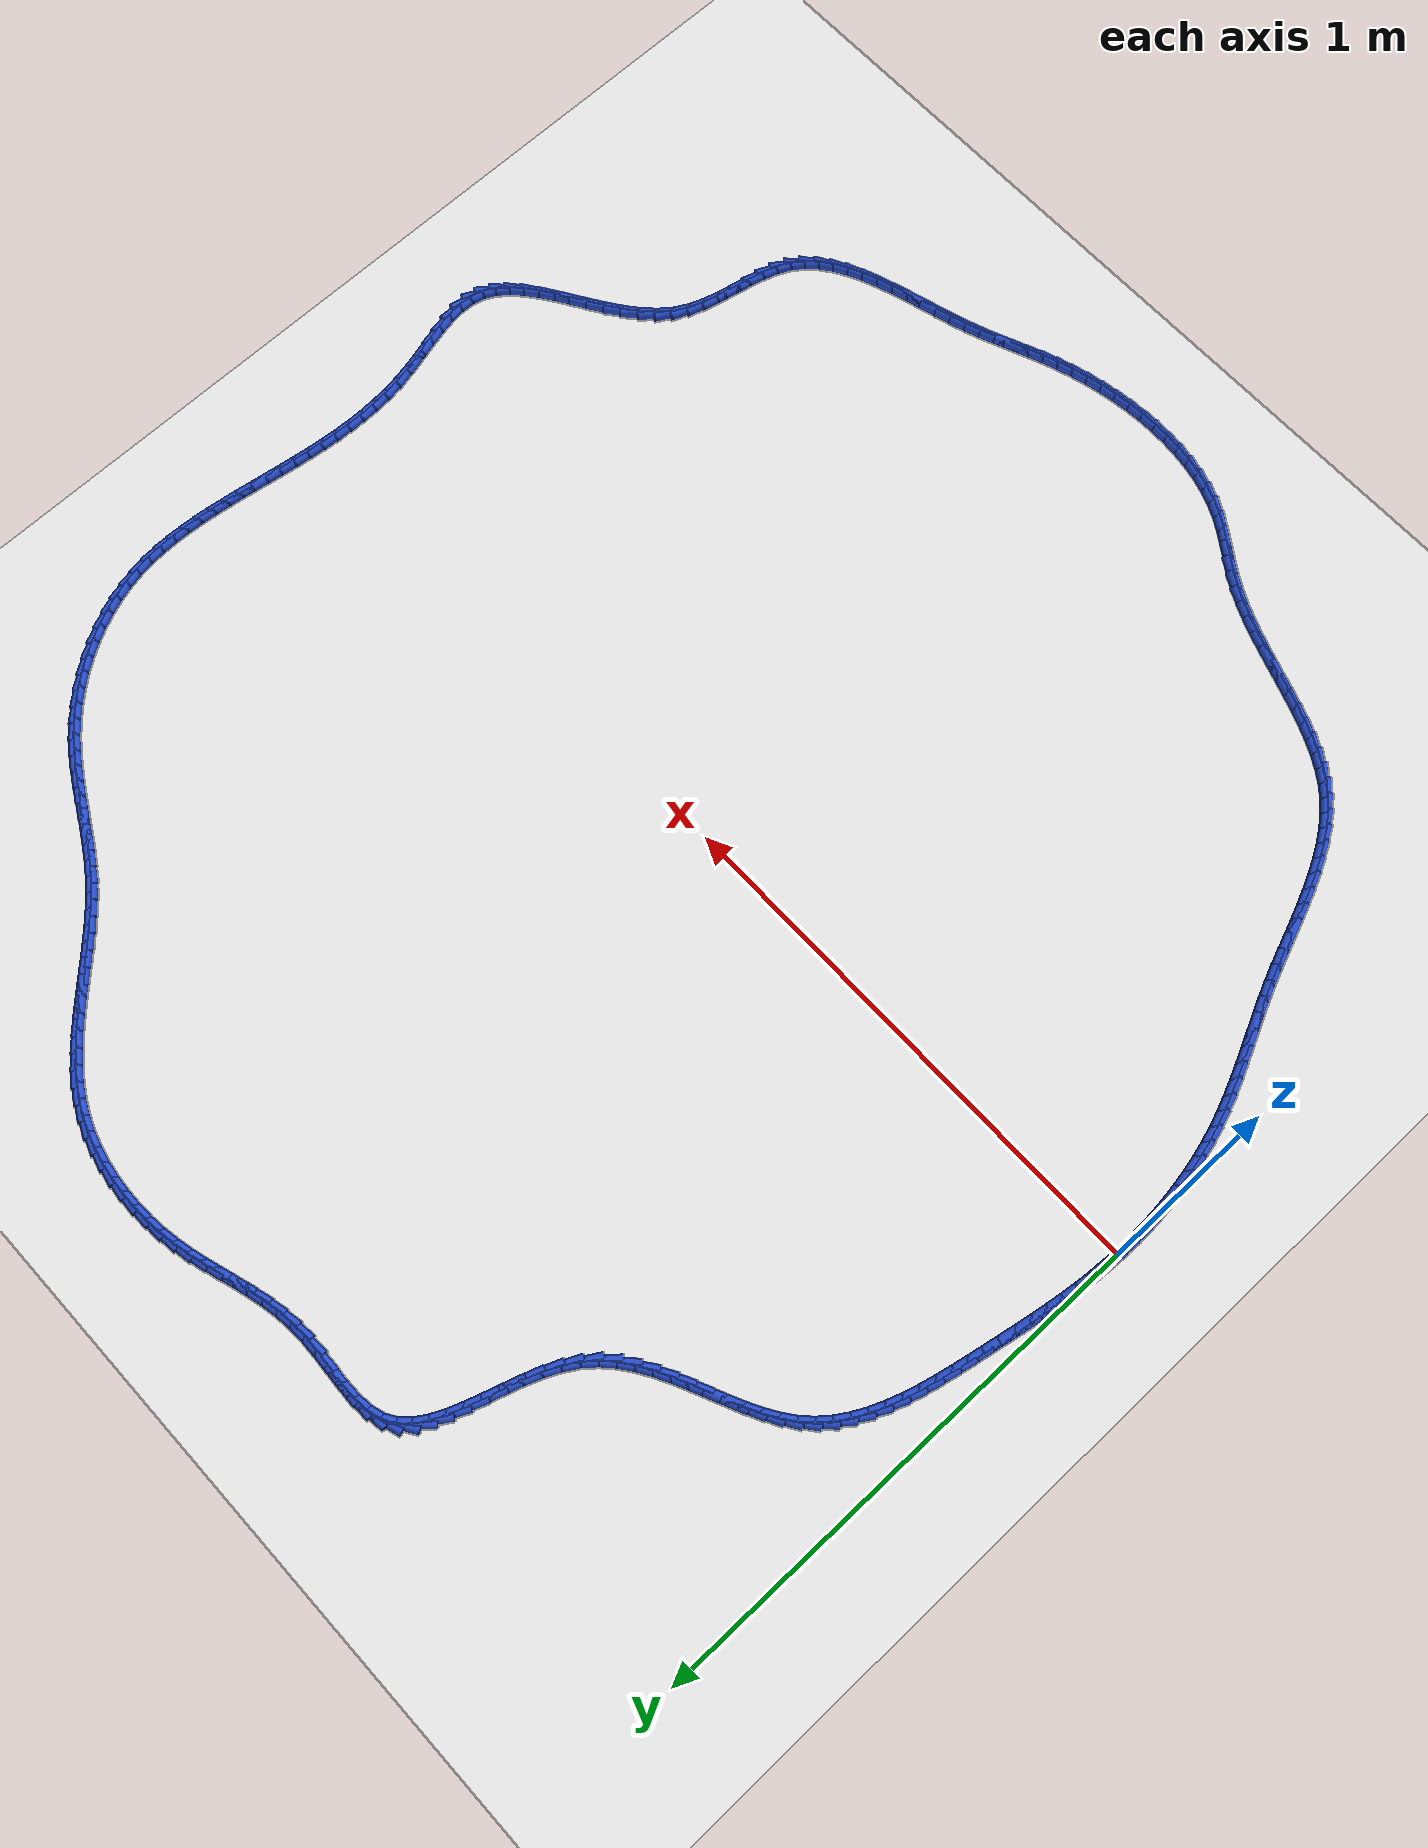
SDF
<sdf version="1.6">
 <world name="default">
  <light name="sun" type="directional">
   <pose>0 0 10 0 -0 0</pose>
   <diffuse>0.8 0.8 0.8 1</diffuse>
   <specular>0.2 0.2 0.2 1</specular>
   <attenuation>
    <range>1000</range>
    <constant>0.9</constant>
    <linear>0.01</linear>
    <quadratic>0.001</quadratic>
   </attenuation>
   <direction>-0.5 0.1 -0.9</direction>
  </light>
  <model name="ground_plane">
   <static>1</static>
   <link name="link">
    <collision name="collision">
     <geometry><plane><normal>0 0 1</normal><size>100 100</size></plane></geometry>
     <surface><friction><ode><mu>100</mu><mu2>50</mu2></ode></friction></surface>
    </collision>
    <visual name="visual">
     <cast_shadows>0</cast_shadows>
     <geometry><plane><normal>0 0 1</normal><size>100 100</size></plane></geometry>
     <material>
      <script><uri>file://media/materials/scripts/gazebo.material</uri><name>Gazebo/WhiteGlow</name></script>
     </material>
    </visual>
   </link>
  </model>
  <gravity>0 0 -9.8</gravity>
  <magnetic_field>6e-06 2.3e-05 -4.2e-05</magnetic_field>
  <atmosphere type="adiabatic"/>
  <physics name="default_physics" default="0" type="ode">
   <max_step_size>0.001</max_step_size>
   <real_time_factor>1</real_time_factor>
   <real_time_update_rate>1000</real_time_update_rate>
  </physics>
  <scene><ambient>0.4 0.4 0.4 1</ambient><background>0.7 0.7 0.7 1</background><shadows>1</shadows></scene>
  <spherical_coordinates>
   <surface_model>EARTH_WGS84</surface_model>
   <latitude_deg>0</latitude_deg>
   <longitude_deg>0</longitude_deg>
   <elevation>0</elevation>
   <heading_deg>0</heading_deg>
  </spherical_coordinates>
  <model name="line">
   <link name="link_0">
    <pose>1.5612511283791264e-17 -2.7755575615628914e-17 0.01 0 1.57 1.5263340523098143</pose>
    <collision name="collision">
     <geometry><cylinder><radius>0.01</radius><length>0.08</length></cylinder></geometry>
    </collision>
    <visual name="visual">
     <material>
      <script><name>Gazebo/Blue</name><uri>file://media/materials/scripts/gazebo.material</uri></script>
     </material>
     <geometry><cylinder><radius>0.01</radius><length>0.08</length></cylinder></geometry>
    </visual>
   </link>
   <link name="link_1">
    <pose>0.0013306014741881163 0.029906804245079018 0.01 0 1.57 1.4944880462793966</pose>
    <collision name="collision">
     <geometry><cylinder><radius>0.01</radius><length>0.08</length></cylinder></geometry>
    </collision>
    <visual name="visual">
     <material>
      <script><name>Gazebo/Blue</name><uri>file://media/materials/scripts/gazebo.material</uri></script>
     </material>
     <geometry><cylinder><radius>0.01</radius><length>0.08</length></cylinder></geometry>
    </visual>
   </link>
   <link name="link_2">
    <pose>0.003603001537472754 0.0596281875780834 0.01 0 1.57 1.4662224820122574</pose>
    <collision name="collision">
     <geometry><cylinder><radius>0.01</radius><length>0.08</length></cylinder></geometry>
    </collision>
    <visual name="visual">
     <material>
      <script><name>Gazebo/Blue</name><uri>file://media/materials/scripts/gazebo.material</uri></script>
     </material>
     <geometry><cylinder><radius>0.01</radius><length>0.08</length></cylinder></geometry>
    </visual>
   </link>
   <link name="link_3">
    <pose>0.0067117343873408725 0.08924737716499878 0.01 0 1.57 1.4418013670284369</pose>
    <collision name="collision">
     <geometry><cylinder><radius>0.01</radius><length>0.08</length></cylinder></geometry>
    </collision>
    <visual name="visual">
     <material>
      <script><name>Gazebo/Blue</name><uri>file://media/materials/scripts/gazebo.material</uri></script>
     </material>
     <geometry><cylinder><radius>0.01</radius><length>0.08</length></cylinder></geometry>
    </visual>
   </link>
   <link name="link_4">
    <pose>0.0105513342212794 0.11884760017181076 0.01 0 1.57 1.4214010598351268</pose>
    <collision name="collision">
     <geometry><cylinder><radius>0.01</radius><length>0.08</length></cylinder></geometry>
    </collision>
    <visual name="visual">
     <material>
      <script><name>Gazebo/Blue</name><uri>file://media/materials/scripts/gazebo.material</uri></script>
     </material>
     <geometry><cylinder><radius>0.01</radius><length>0.08</length></cylinder></geometry>
    </visual>
   </link>
   <link name="link_5">
    <pose>0.015016335236775286 0.148512083764505 0.01 0 1.57 1.4051165456496912</pose>
    <collision name="collision">
     <geometry><cylinder><radius>0.01</radius><length>0.08</length></cylinder></geometry>
    </collision>
    <visual name="visual">
     <material>
      <script><name>Gazebo/Blue</name><uri>file://media/materials/scripts/gazebo.material</uri></script>
     </material>
     <geometry><cylinder><radius>0.01</radius><length>0.08</length></cylinder></geometry>
    </visual>
   </link>
   <link name="link_6">
    <pose>0.020001271631315463 0.1783240551090671 0.01 0 1.57 1.3929702809782907</pose>
    <collision name="collision">
     <geometry><cylinder><radius>0.01</radius><length>0.08</length></cylinder></geometry>
    </collision>
    <visual name="visual">
     <material>
      <script><name>Gazebo/Blue</name><uri>file://media/materials/scripts/gazebo.material</uri></script>
     </material>
     <geometry><cylinder><radius>0.01</radius><length>0.08</length></cylinder></geometry>
    </visual>
   </link>
   <link name="link_7">
    <pose>0.02540067760238686 0.2083667413714826 0.01 0 1.57 1.3849220156373319</pose>
    <collision name="collision">
     <geometry><cylinder><radius>0.01</radius><length>0.08</length></cylinder></geometry>
    </collision>
    <visual name="visual">
     <material>
      <script><name>Gazebo/Blue</name><uri>file://media/materials/scripts/gazebo.material</uri></script>
     </material>
     <geometry><cylinder><radius>0.01</radius><length>0.08</length></cylinder></geometry>
    </visual>
   </link>
   <link name="link_8">
    <pose>0.03110908734747644 0.23872336971773733 0.01 0 1.57 1.3808784082332122</pose>
    <collision name="collision">
     <geometry><cylinder><radius>0.01</radius><length>0.08</length></cylinder></geometry>
    </collision>
    <visual name="visual">
     <material>
      <script><name>Gazebo/Blue</name><uri>file://media/materials/scripts/gazebo.material</uri></script>
     </material>
     <geometry><cylinder><radius>0.01</radius><length>0.08</length></cylinder></geometry>
    </visual>
   </link>
   <link name="link_9">
    <pose>0.03702103506407113 0.26947716731381677 0.01 0 1.57 1.3785720279207565</pose>
    <collision name="collision">
     <geometry><cylinder><radius>0.01</radius><length>0.08</length></cylinder></geometry>
    </collision>
    <visual name="visual">
     <material>
      <script><name>Gazebo/Blue</name><uri>file://media/materials/scripts/gazebo.material</uri></script>
     </material>
     <geometry><cylinder><radius>0.01</radius><length>0.08</length></cylinder></geometry>
    </visual>
   </link>
   <link name="link_10">
    <pose>0.04308827736458533 0.30065079643314907 0.01 0 1.57 1.3692006358391113</pose>
    <collision name="collision">
     <geometry><cylinder><radius>0.01</radius><length>0.08</length></cylinder></geometry>
    </collision>
    <visual name="visual">
     <material>
      <script><name>Gazebo/Blue</name><uri>file://media/materials/scripts/gazebo.material</uri></script>
     </material>
     <geometry><cylinder><radius>0.01</radius><length>0.08</length></cylinder></geometry>
    </visual>
   </link>
   <link name="link_11">
    <pose>0.049498655112997 0.3320170449363359 0.01 0 1.57 1.3504834893484938</pose>
    <collision name="collision">
     <geometry><cylinder><radius>0.01</radius><length>0.08</length></cylinder></geometry>
    </collision>
    <visual name="visual">
     <material>
      <script><name>Gazebo/Blue</name><uri>file://media/materials/scripts/gazebo.material</uri></script>
     </material>
     <geometry><cylinder><radius>0.01</radius><length>0.08</length></cylinder></geometry>
    </visual>
   </link>
   <link name="link_12">
    <pose>0.0565008850613548 0.36328426891148163 0.01 0 1.57 1.3220518338765654</pose>
    <collision name="collision">
     <geometry><cylinder><radius>0.01</radius><length>0.08</length></cylinder></geometry>
    </collision>
    <visual name="visual">
     <material>
      <script><name>Gazebo/Blue</name><uri>file://media/materials/scripts/gazebo.material</uri></script>
     </material>
     <geometry><cylinder><radius>0.01</radius><length>0.08</length></cylinder></geometry>
    </visual>
   </link>
   <link name="link_13">
    <pose>0.06434368402650485 0.39416082437810845 0.01 0 1.57 1.283178066715591</pose>
    <collision name="collision">
     <geometry><cylinder><radius>0.01</radius><length>0.08</length></cylinder></geometry>
    </collision>
    <visual name="visual">
     <material>
      <script><name>Gazebo/Blue</name><uri>file://media/materials/scripts/gazebo.material</uri></script>
     </material>
     <geometry><cylinder><radius>0.01</radius><length>0.08</length></cylinder></geometry>
    </visual>
   </link>
   <link name="link_14">
    <pose>0.07327576882529341 0.4243550673557384 0.01 0 1.57 1.2328115154408856</pose>
    <collision name="collision">
     <geometry><cylinder><radius>0.01</radius><length>0.08</length></cylinder></geometry>
    </collision>
    <visual name="visual">
     <material>
      <script><name>Gazebo/Blue</name><uri>file://media/materials/scripts/gazebo.material</uri></script>
     </material>
     <geometry><cylinder><radius>0.01</radius><length>0.08</length></cylinder></geometry>
    </visual>
   </link>
   <link name="link_15">
    <pose>0.08354585627456658 0.4535753538638936 0.01 0 1.57 1.1696511075530047</pose>
    <collision name="collision">
     <geometry><cylinder><radius>0.01</radius><length>0.08</length></cylinder></geometry>
    </collision>
    <visual name="visual">
     <material>
      <script><name>Gazebo/Blue</name><uri>file://media/materials/scripts/gazebo.material</uri></script>
     </material>
     <geometry><cylinder><radius>0.01</radius><length>0.08</length></cylinder></geometry>
    </visual>
   </link>
   <link name="link_16">
    <pose>0.09540266319117052 0.48153003992209603 0.01 0 1.57 1.0923041557974338</pose>
    <collision name="collision">
     <geometry><cylinder><radius>0.01</radius><length>0.08</length></cylinder></geometry>
    </collision>
    <visual name="visual">
     <material>
      <script><name>Gazebo/Blue</name><uri>file://media/materials/scripts/gazebo.material</uri></script>
     </material>
     <geometry><cylinder><radius>0.01</radius><length>0.08</length></cylinder></geometry>
    </visual>
   </link>
   <link name="link_17">
    <pose>0.10909490639195141 0.5079274815498676 0.01 0 1.57 0.9995976883542236</pose>
    <collision name="collision">
     <geometry><cylinder><radius>0.01</radius><length>0.08</length></cylinder></geometry>
    </collision>
    <visual name="visual">
     <material>
      <script><name>Gazebo/Blue</name><uri>file://media/materials/scripts/gazebo.material</uri></script>
     </material>
     <geometry><cylinder><radius>0.01</radius><length>0.08</length></cylinder></geometry>
    </visual>
   </link>
   <link name="link_18">
    <pose>0.1248713026937554 0.5324760347667303 0.01 0 1.57 0.8910995392675002</pose>
    <collision name="collision">
     <geometry><cylinder><radius>0.01</radius><length>0.08</length></cylinder></geometry>
    </collision>
    <visual name="visual">
     <material>
      <script><name>Gazebo/Blue</name><uri>file://media/materials/scripts/gazebo.material</uri></script>
     </material>
     <geometry><cylinder><radius>0.01</radius><length>0.08</length></cylinder></geometry>
    </visual>
   </link>
   <link name="link_19">
    <pose>0.1429805689134286 0.5548840555922063 0.01 0 1.57 0.7683180647985376</pose>
    <collision name="collision">
     <geometry><cylinder><radius>0.01</radius><length>0.08</length></cylinder></geometry>
    </collision>
    <visual name="visual">
     <material>
      <script><name>Gazebo/Blue</name><uri>file://media/materials/scripts/gazebo.material</uri></script>
     </material>
     <geometry><cylinder><radius>0.01</radius><length>0.08</length></cylinder></geometry>
    </visual>
   </link>
   <link name="link_20">
    <pose>0.16366161804433552 0.5748704335060205 0.01 0 1.57 0.6501714459752197</pose>
    <collision name="collision">
     <geometry><cylinder><radius>0.01</radius><length>0.08</length></cylinder></geometry>
    </collision>
    <visual name="visual">
     <material>
      <script><name>Gazebo/Blue</name><uri>file://media/materials/scripts/gazebo.material</uri></script>
     </material>
     <geometry><cylinder><radius>0.01</radius><length>0.08</length></cylinder></geometry>
    </visual>
   </link>
   <link name="link_21">
    <pose>0.1868365829656764 0.5924944140471236 0.01 0 1.57 0.5576966939674891</pose>
    <collision name="collision">
     <geometry><cylinder><radius>0.01</radius><length>0.08</length></cylinder></geometry>
    </collision>
    <visual name="visual">
     <material>
      <script><name>Gazebo/Blue</name><uri>file://media/materials/scripts/gazebo.material</uri></script>
     </material>
     <geometry><cylinder><radius>0.01</radius><length>0.08</length></cylinder></geometry>
    </visual>
   </link>
   <link name="link_22">
    <pose>0.2120498657321334 0.6082210857008276 0.01 0 1.57 0.491084931968654</pose>
    <collision name="collision">
     <geometry><cylinder><radius>0.01</radius><length>0.08</length></cylinder></geometry>
    </collision>
    <visual name="visual">
     <material>
      <script><name>Gazebo/Blue</name><uri>file://media/materials/scripts/gazebo.material</uri></script>
     </material>
     <geometry><cylinder><radius>0.01</radius><length>0.08</length></cylinder></geometry>
    </visual>
   </link>
   <link name="link_23">
    <pose>0.23882375597604882 0.622539295062853 0.01 0 1.57 0.4483172115358521</pose>
    <collision name="collision">
     <geometry><cylinder><radius>0.01</radius><length>0.08</length></cylinder></geometry>
    </collision>
    <visual name="visual">
     <material>
      <script><name>Gazebo/Blue</name><uri>file://media/materials/scripts/gazebo.material</uri></script>
     </material>
     <geometry><cylinder><radius>0.01</radius><length>0.08</length></cylinder></geometry>
    </visual>
   </link>
   <link name="link_24">
    <pose>0.26668054332976476 0.6359378887289207 0.01 0 1.57 0.42751709651057657</pose>
    <collision name="collision">
     <geometry><cylinder><radius>0.01</radius><length>0.08</length></cylinder></geometry>
    </collision>
    <visual name="visual">
     <material>
      <script><name>Gazebo/Blue</name><uri>file://media/materials/scripts/gazebo.material</uri></script>
     </material>
     <geometry><cylinder><radius>0.01</radius><length>0.08</length></cylinder></geometry>
    </visual>
   </link>
   <link name="link_25">
    <pose>0.2951425174256238 0.6489057132947512 0.01 0 1.57 0.4275170038117735</pose>
    <collision name="collision">
     <geometry><cylinder><radius>0.01</radius><length>0.08</length></cylinder></geometry>
    </collision>
    <visual name="visual">
     <material>
      <script><name>Gazebo/Blue</name><uri>file://media/materials/scripts/gazebo.material</uri></script>
     </material>
     <geometry><cylinder><radius>0.01</radius><length>0.08</length></cylinder></geometry>
    </visual>
   </link>
   <link name="link_26">
    <pose>0.3237319678959679 0.6619316153560653 0.01 0 1.57 0.44803796307908167</pose>
    <collision name="collision">
     <geometry><cylinder><radius>0.01</radius><length>0.08</length></cylinder></geometry>
    </collision>
    <visual name="visual">
     <material>
      <script><name>Gazebo/Blue</name><uri>file://media/materials/scripts/gazebo.material</uri></script>
     </material>
     <geometry><cylinder><radius>0.01</radius><length>0.08</length></cylinder></geometry>
    </visual>
   </link>
   <link name="link_27">
    <pose>0.3519711843731395 0.6755044415085835 0.01 0 1.57 0.48965199902746565</pose>
    <collision name="collision">
     <geometry><cylinder><radius>0.01</radius><length>0.08</length></cylinder></geometry>
    </collision>
    <visual name="visual">
     <material>
      <script><name>Gazebo/Blue</name><uri>file://media/materials/scripts/gazebo.material</uri></script>
     </material>
     <geometry><cylinder><radius>0.01</radius><length>0.08</length></cylinder></geometry>
    </visual>
   </link>
   <link name="link_28">
    <pose>0.3793824564894808 0.6901130383480265 0.01 0 1.57 0.5535481722904566</pose>
    <collision name="collision">
     <geometry><cylinder><radius>0.01</radius><length>0.08</length></cylinder></geometry>
    </collision>
    <visual name="visual">
     <material>
      <script><name>Gazebo/Blue</name><uri>file://media/materials/scripts/gazebo.material</uri></script>
     </material>
     <geometry><cylinder><radius>0.01</radius><length>0.08</length></cylinder></geometry>
    </visual>
   </link>
   <link name="link_29">
    <pose>0.40548807387733404 0.7062462524701151 0.01 0 1.57 0.6409963537998252</pose>
    <collision name="collision">
     <geometry><cylinder><radius>0.01</radius><length>0.08</length></cylinder></geometry>
    </collision>
    <visual name="visual">
     <material>
      <script><name>Gazebo/Blue</name><uri>file://media/materials/scripts/gazebo.material</uri></script>
     </material>
     <geometry><cylinder><radius>0.01</radius><length>0.08</length></cylinder></geometry>
    </visual>
   </link>
   <link name="link_30">
    <pose>0.4298103261690416 0.7243929304705699 0.01 0 1.57 0.752345749485207</pose>
    <collision name="collision">
     <geometry><cylinder><radius>0.01</radius><length>0.08</length></cylinder></geometry>
    </collision>
    <visual name="visual">
     <material>
      <script><name>Gazebo/Blue</name><uri>file://media/materials/scripts/gazebo.material</uri></script>
     </material>
     <geometry><cylinder><radius>0.01</radius><length>0.08</length></cylinder></geometry>
    </visual>
   </link>
   <link name="link_31">
    <pose>0.4518715029969457 0.7450419189451114 0.01 0 1.57 0.8855622930854772</pose>
    <collision name="collision">
     <geometry><cylinder><radius>0.01</radius><length>0.08</length></cylinder></geometry>
    </collision>
    <visual name="visual">
     <material>
      <script><name>Gazebo/Blue</name><uri>file://media/materials/scripts/gazebo.material</uri></script>
     </material>
     <geometry><cylinder><radius>0.01</radius><length>0.08</length></cylinder></geometry>
    </visual>
   </link>
   <link name="link_32">
    <pose>0.4711938939933884 0.7686820644894603 0.01 0 1.57 1.0264599800984286</pose>
    <collision name="collision">
     <geometry><cylinder><radius>0.01</radius><length>0.08</length></cylinder></geometry>
    </collision>
    <visual name="visual">
     <material>
      <script><name>Gazebo/Blue</name><uri>file://media/materials/scripts/gazebo.material</uri></script>
     </material>
     <geometry><cylinder><radius>0.01</radius><length>0.08</length></cylinder></geometry>
    </visual>
   </link>
   <link name="link_33">
    <pose>0.4874807825842777 0.7955874439428817 0.01 0 1.57 1.1356766998835106</pose>
    <collision name="collision">
     <geometry><cylinder><radius>0.01</radius><length>0.08</length></cylinder></geometry>
    </collision>
    <visual name="visual">
     <material>
      <script><name>Gazebo/Blue</name><uri>file://media/materials/scripts/gazebo.material</uri></script>
     </material>
     <geometry><cylinder><radius>0.01</radius><length>0.08</length></cylinder></geometry>
    </visual>
   </link>
   <link name="link_34">
    <pose>0.501206925812297 0.8251166928053337 0.01 0 1.57 1.2086594481735204</pose>
    <collision name="collision">
     <geometry><cylinder><radius>0.01</radius><length>0.08</length></cylinder></geometry>
    </collision>
    <visual name="visual">
     <material>
      <script><name>Gazebo/Blue</name><uri>file://media/materials/scripts/gazebo.material</uri></script>
     </material>
     <geometry><cylinder><radius>0.01</radius><length>0.08</length></cylinder></geometry>
    </visual>
   </link>
   <link name="link_35">
    <pose>0.5130525925730723 0.8563845833495595 0.01 0 1.57 1.2507738367512033</pose>
    <collision name="collision">
     <geometry><cylinder><radius>0.01</radius><length>0.08</length></cylinder></geometry>
    </collision>
    <visual name="visual">
     <material>
      <script><name>Gazebo/Blue</name><uri>file://media/materials/scripts/gazebo.material</uri></script>
     </material>
     <geometry><cylinder><radius>0.01</radius><length>0.08</length></cylinder></geometry>
    </visual>
   </link>
   <link name="link_36">
    <pose>0.5236980535949607 0.8885058856735554 0.01 0 1.57 1.265144034899009</pose>
    <collision name="collision">
     <geometry><cylinder><radius>0.01</radius><length>0.08</length></cylinder></geometry>
    </collision>
    <visual name="visual">
     <material>
      <script><name>Gazebo/Blue</name><uri>file://media/materials/scripts/gazebo.material</uri></script>
     </material>
     <geometry><cylinder><radius>0.01</radius><length>0.08</length></cylinder></geometry>
    </visual>
   </link>
   <link name="link_37">
    <pose>0.5338235796063195 0.920595369875319 0.01 0 1.57 1.2520789169894673</pose>
    <collision name="collision">
     <geometry><cylinder><radius>0.01</radius><length>0.08</length></cylinder></geometry>
    </collision>
    <visual name="visual">
     <material>
      <script><name>Gazebo/Blue</name><uri>file://media/materials/scripts/gazebo.material</uri></script>
     </material>
     <geometry><cylinder><radius>0.01</radius><length>0.08</length></cylinder></geometry>
    </visual>
   </link>
   <link name="link_38">
    <pose>0.5441094413355054 0.9517678060528469 0.01 0 1.57 1.2086669883868508</pose>
    <collision name="collision">
     <geometry><cylinder><radius>0.01</radius><length>0.08</length></cylinder></geometry>
    </collision>
    <visual name="visual">
     <material>
      <script><name>Gazebo/Blue</name><uri>file://media/materials/scripts/gazebo.material</uri></script>
     </material>
     <geometry><cylinder><radius>0.01</radius><length>0.08</length></cylinder></geometry>
    </visual>
   </link>
   <link name="link_39">
    <pose>0.5552359095108762 0.9811379643041374 0.01 0 1.57 1.128171284352991</pose>
    <collision name="collision">
     <geometry><cylinder><radius>0.01</radius><length>0.08</length></cylinder></geometry>
    </collision>
    <visual name="visual">
     <material>
      <script><name>Gazebo/Blue</name><uri>file://media/materials/scripts/gazebo.material</uri></script>
     </material>
     <geometry><cylinder><radius>0.01</radius><length>0.08</length></cylinder></geometry>
    </visual>
   </link>
   <link name="link_40">
    <pose>0.5678832548607885 1.0078206147271869 0.01 0 1.57 0.9997001301491173</pose>
    <collision name="collision">
     <geometry><cylinder><radius>0.01</radius><length>0.08</length></cylinder></geometry>
    </collision>
    <visual name="visual">
     <material>
      <script><name>Gazebo/Blue</name><uri>file://media/materials/scripts/gazebo.material</uri></script>
     </material>
     <geometry><cylinder><radius>0.01</radius><length>0.08</length></cylinder></geometry>
    </visual>
   </link>
   <link name="link_41">
    <pose>0.5827317481135997 1.030930527419993 0.01 0 1.57 0.8107359534185179</pose>
    <collision name="collision">
     <geometry><cylinder><radius>0.01</radius><length>0.08</length></cylinder></geometry>
    </collision>
    <visual name="visual">
     <material>
      <script><name>Gazebo/Blue</name><uri>file://media/materials/scripts/gazebo.material</uri></script>
     </material>
     <geometry><cylinder><radius>0.01</radius><length>0.08</length></cylinder></geometry>
    </visual>
   </link>
   <link name="link_42">
    <pose>0.6004616599976669 1.0495824724805525 0.01 0 1.57 0.5587837810290953</pose>
    <collision name="collision">
     <geometry><cylinder><radius>0.01</radius><length>0.08</length></cylinder></geometry>
    </collision>
    <visual name="visual">
     <material>
      <script><name>Gazebo/Blue</name><uri>file://media/materials/scripts/gazebo.material</uri></script>
     </material>
     <geometry><cylinder><radius>0.01</radius><length>0.08</length></cylinder></geometry>
    </visual>
   </link>
   <link name="link_43">
    <pose>0.6217513968691741 1.0628940199535446 0.01 0 1.57 0.2980568340622645</pose>
    <collision name="collision">
     <geometry><cylinder><radius>0.01</radius><length>0.08</length></cylinder></geometry>
    </collision>
    <visual name="visual">
     <material>
      <script><name>Gazebo/Blue</name><uri>file://media/materials/scripts/gazebo.material</uri></script>
     </material>
     <geometry><cylinder><radius>0.01</radius><length>0.08</length></cylinder></geometry>
    </visual>
   </link>
   <link name="link_44">
    <pose>0.6468627392782944 1.0706084357935222 0.01 0 1.57 0.11531449839824548</pose>
    <collision name="collision">
     <geometry><cylinder><radius>0.01</radius><length>0.08</length></cylinder></geometry>
    </collision>
    <visual name="visual">
     <material>
      <script><name>Gazebo/Blue</name><uri>file://media/materials/scripts/gazebo.material</uri></script>
     </material>
     <geometry><cylinder><radius>0.01</radius><length>0.08</length></cylinder></geometry>
    </visual>
   </link>
   <link name="link_45">
    <pose>0.6751171955826861 1.0738811031511761 0.01 0 1.57 0.005880650860963544</pose>
    <collision name="collision">
     <geometry><cylinder><radius>0.01</radius><length>0.08</length></cylinder></geometry>
    </collision>
    <visual name="visual">
     <material>
      <script><name>Gazebo/Blue</name><uri>file://media/materials/scripts/gazebo.material</uri></script>
     </material>
     <geometry><cylinder><radius>0.01</radius><length>0.08</length></cylinder></geometry>
    </visual>
   </link>
   <link name="link_46">
    <pose>0.7057073702022806 1.0740609953615754 0.01 0 1.57 -0.04865344051061675</pose>
    <collision name="collision">
     <geometry><cylinder><radius>0.01</radius><length>0.08</length></cylinder></geometry>
    </collision>
    <visual name="visual">
     <material>
      <script><name>Gazebo/Blue</name><uri>file://media/materials/scripts/gazebo.material</uri></script>
     </material>
     <geometry><cylinder><radius>0.01</radius><length>0.08</length></cylinder></geometry>
    </visual>
   </link>
   <link name="link_47">
    <pose>0.7378258675570086 1.0724970857597906 0.01 0 1.57 -0.05957534966952704</pose>
    <collision name="collision">
     <geometry><cylinder><radius>0.01</radius><length>0.08</length></cylinder></geometry>
    </collision>
    <visual name="visual">
     <material>
      <script><name>Gazebo/Blue</name><uri>file://media/materials/scripts/gazebo.material</uri></script>
     </material>
     <geometry><cylinder><radius>0.01</radius><length>0.08</length></cylinder></geometry>
    </visual>
   </link>
   <link name="link_48">
    <pose>0.7706652920668017 1.070538347680891 0.01 0 1.57 -0.030662220794457115</pose>
    <collision name="collision">
     <geometry><cylinder><radius>0.01</radius><length>0.08</length></cylinder></geometry>
    </collision>
    <visual name="visual">
     <material>
      <script><name>Gazebo/Blue</name><uri>file://media/materials/scripts/gazebo.material</uri></script>
     </material>
     <geometry><cylinder><radius>0.01</radius><length>0.08</length></cylinder></geometry>
    </visual>
   </link>
   <link name="link_49">
    <pose>0.8034182481515902 1.0695337544599464 0.01 0 1.57 0.039172706857328994</pose>
    <collision name="collision">
     <geometry><cylinder><radius>0.01</radius><length>0.08</length></cylinder></geometry>
    </collision>
    <visual name="visual">
     <material>
      <script><name>Gazebo/Blue</name><uri>file://media/materials/scripts/gazebo.material</uri></script>
     </material>
     <geometry><cylinder><radius>0.01</radius><length>0.08</length></cylinder></geometry>
    </visual>
   </link>
   <link name="link_50">
    <pose>0.8353042205179027 1.0707834535952234 0.01 0 1.57 0.1245799160838165</pose>
    <collision name="collision">
     <geometry><cylinder><radius>0.01</radius><length>0.08</length></cylinder></geometry>
    </collision>
    <visual name="visual">
     <material>
      <script><name>Gazebo/Blue</name><uri>file://media/materials/scripts/gazebo.material</uri></script>
     </material>
     <geometry><cylinder><radius>0.01</radius><length>0.08</length></cylinder></geometry>
    </visual>
   </link>
   <link name="link_51">
    <pose>0.8660666935266311 1.0746357901733288 0.01 0 1.57 0.1963043708164726</pose>
    <collision name="collision">
     <geometry><cylinder><radius>0.01</radius><length>0.08</length></cylinder></geometry>
    </collision>
    <visual name="visual">
     <material>
      <script><name>Gazebo/Blue</name><uri>file://media/materials/scripts/gazebo.material</uri></script>
     </material>
     <geometry><cylinder><radius>0.01</radius><length>0.08</length></cylinder></geometry>
    </visual>
   </link>
   <link name="link_52">
    <pose>0.8959255929759979 1.0805736924713536 0.01 0 1.57 0.2506689041640947</pose>
    <collision name="collision">
     <geometry><cylinder><radius>0.01</radius><length>0.08</length></cylinder></geometry>
    </collision>
    <visual name="visual">
     <material>
      <script><name>Gazebo/Blue</name><uri>file://media/materials/scripts/gazebo.material</uri></script>
     </material>
     <geometry><cylinder><radius>0.01</radius><length>0.08</length></cylinder></geometry>
    </visual>
   </link>
   <link name="link_53">
    <pose>0.92511818630646 1.0880485890950398 0.01 0 1.57 0.28616184921676585</pose>
    <collision name="collision">
     <geometry><cylinder><radius>0.01</radius><length>0.08</length></cylinder></geometry>
    </collision>
    <visual name="visual">
     <material>
      <script><name>Gazebo/Blue</name><uri>file://media/materials/scripts/gazebo.material</uri></script>
     </material>
     <geometry><cylinder><radius>0.01</radius><length>0.08</length></cylinder></geometry>
    </visual>
   </link>
   <link name="link_54">
    <pose>0.9538817409584741 1.0965119086501285 0.01 0 1.57 0.3020712178301751</pose>
    <collision name="collision">
     <geometry><cylinder><radius>0.01</radius><length>0.08</length></cylinder></geometry>
    </collision>
    <visual name="visual">
     <material>
      <script><name>Gazebo/Blue</name><uri>file://media/materials/scripts/gazebo.material</uri></script>
     </material>
     <geometry><cylinder><radius>0.01</radius><length>0.08</length></cylinder></geometry>
    </visual>
   </link>
   <link name="link_55">
    <pose>0.982453524372497 1.1054150797423623 0.01 0 1.57 0.2981520466221401</pose>
    <collision name="collision">
     <geometry><cylinder><radius>0.01</radius><length>0.08</length></cylinder></geometry>
    </collision>
    <visual name="visual">
     <material>
      <script><name>Gazebo/Blue</name><uri>file://media/materials/scripts/gazebo.material</uri></script>
     </material>
     <geometry><cylinder><radius>0.01</radius><length>0.08</length></cylinder></geometry>
    </visual>
   </link>
   <link name="link_56">
    <pose>1.0110708039889853 1.1142095309774813 0.01 0 1.57 0.2744567494896787</pose>
    <collision name="collision">
     <geometry><cylinder><radius>0.01</radius><length>0.08</length></cylinder></geometry>
    </collision>
    <visual name="visual">
     <material>
      <script><name>Gazebo/Blue</name><uri>file://media/materials/scripts/gazebo.material</uri></script>
     </material>
     <geometry><cylinder><radius>0.01</radius><length>0.08</length></cylinder></geometry>
    </visual>
   </link>
   <link name="link_57">
    <pose>1.0399708472483955 1.122346690961228 0.01 0 1.57 0.23137815917745772</pose>
    <collision name="collision">
     <geometry><cylinder><radius>0.01</radius><length>0.08</length></cylinder></geometry>
    </collision>
    <visual name="visual">
     <material>
      <script><name>Gazebo/Blue</name><uri>file://media/materials/scripts/gazebo.material</uri></script>
     </material>
     <geometry><cylinder><radius>0.01</radius><length>0.08</length></cylinder></geometry>
    </visual>
   </link>
   <link name="link_58">
    <pose>1.069390921591184 1.1292779882993433 0.01 0 1.57 0.17248066126663625</pose>
    <collision name="collision">
     <geometry><cylinder><radius>0.01</radius><length>0.08</length></cylinder></geometry>
    </collision>
    <visual name="visual">
     <material>
      <script><name>Gazebo/Blue</name><uri>file://media/materials/scripts/gazebo.material</uri></script>
     </material>
     <geometry><cylinder><radius>0.01</radius><length>0.08</length></cylinder></geometry>
    </visual>
   </link>
   <link name="link_59">
    <pose>1.0995034604607472 1.1345239440414097 0.01 0 1.57 0.1107858189988246</pose>
    <collision name="collision">
     <geometry><cylinder><radius>0.01</radius><length>0.08</length></cylinder></geometry>
    </collision>
    <visual name="visual">
     <material>
      <script><name>Gazebo/Blue</name><uri>file://media/materials/scripts/gazebo.material</uri></script>
     </material>
     <geometry><cylinder><radius>0.01</radius><length>0.08</length></cylinder></geometry>
    </visual>
   </link>
   <link name="link_60">
    <pose>1.1301709068327124 1.1379354305951885 0.01 0 1.57 0.04921476953226253</pose>
    <collision name="collision">
     <geometry><cylinder><radius>0.01</radius><length>0.08</length></cylinder></geometry>
    </collision>
    <visual name="visual">
     <material>
      <script><name>Gazebo/Blue</name><uri>file://media/materials/scripts/gazebo.material</uri></script>
     </material>
     <geometry><cylinder><radius>0.01</radius><length>0.08</length></cylinder></geometry>
    </visual>
   </link>
   <link name="link_61">
    <pose>1.1611631624159011 1.1394619399595434 0.01 0 1.57 -0.013154551290990045</pose>
    <collision name="collision">
     <geometry><cylinder><radius>0.01</radius><length>0.08</length></cylinder></geometry>
    </collision>
    <visual name="visual">
     <material>
      <script><name>Gazebo/Blue</name><uri>file://media/materials/scripts/gazebo.material</uri></script>
     </material>
     <geometry><cylinder><radius>0.01</radius><length>0.08</length></cylinder></geometry>
    </visual>
   </link>
   <link name="link_62">
    <pose>1.1922501126330498 1.1390529814891321 0.01 0 1.57 -0.07722249879751826</pose>
    <collision name="collision">
     <geometry><cylinder><radius>0.01</radius><length>0.08</length></cylinder></geometry>
    </collision>
    <visual name="visual">
     <material>
      <script><name>Gazebo/Blue</name><uri>file://media/materials/scripts/gazebo.material</uri></script>
     </material>
     <geometry><cylinder><radius>0.01</radius><length>0.08</length></cylinder></geometry>
    </visual>
   </link>
   <link name="link_63">
    <pose>1.223201642906896 1.1366580645386113 0.01 0 1.57 -0.14388103662224003</pose>
    <collision name="collision">
     <geometry><cylinder><radius>0.01</radius><length>0.08</length></cylinder></geometry>
    </collision>
    <visual name="visual">
     <material>
      <script><name>Gazebo/Blue</name><uri>file://media/materials/scripts/gazebo.material</uri></script>
     </material>
     <geometry><cylinder><radius>0.01</radius><length>0.08</length></cylinder></geometry>
    </visual>
   </link>
   <link name="link_64">
    <pose>1.2537876386601752 1.1322266984626381 0.01 0 1.57 -0.21401818619725188</pose>
    <collision name="collision">
     <geometry><cylinder><radius>0.01</radius><length>0.08</length></cylinder></geometry>
    </collision>
    <visual name="visual">
     <material>
      <script><name>Gazebo/Blue</name><uri>file://media/materials/scripts/gazebo.material</uri></script>
     </material>
     <geometry><cylinder><radius>0.01</radius><length>0.08</length></cylinder></geometry>
    </visual>
   </link>
   <link name="link_65">
    <pose>1.2837779853156241 1.125708392615869 0.01 0 1.57 -0.2885086044313413</pose>
    <collision name="collision">
     <geometry><cylinder><radius>0.01</radius><length>0.08</length></cylinder></geometry>
    </collision>
    <visual name="visual">
     <material>
      <script><name>Gazebo/Blue</name><uri>file://media/materials/scripts/gazebo.material</uri></script>
     </material>
     <geometry><cylinder><radius>0.01</radius><length>0.08</length></cylinder></geometry>
    </visual>
   </link>
   <link name="link_66">
    <pose>1.3129425682959803 1.1170526563529617 0.01 0 1.57 -0.3681842953426652</pose>
    <collision name="collision">
     <geometry><cylinder><radius>0.01</radius><length>0.08</length></cylinder></geometry>
    </collision>
    <visual name="visual">
     <material>
      <script><name>Gazebo/Blue</name><uri>file://media/materials/scripts/gazebo.material</uri></script>
     </material>
     <geometry><cylinder><radius>0.01</radius><length>0.08</length></cylinder></geometry>
    </visual>
   </link>
   <link name="link_67">
    <pose>1.3410512730239799 1.1062089990285733 0.01 0 1.57 -0.453066055847872</pose>
    <collision name="collision">
     <geometry><cylinder><radius>0.01</radius><length>0.08</length></cylinder></geometry>
    </collision>
    <visual name="visual">
     <material>
      <script><name>Gazebo/Blue</name><uri>file://media/materials/scripts/gazebo.material</uri></script>
     </material>
     <geometry><cylinder><radius>0.01</radius><length>0.08</length></cylinder></geometry>
    </visual>
   </link>
   <link name="link_68">
    <pose>1.3678921469280785 1.093141729395896 0.01 0 1.57 -0.5343116861021012</pose>
    <collision name="collision">
     <geometry><cylinder><radius>0.01</radius><length>0.08</length></cylinder></geometry>
    </collision>
    <visual name="visual">
     <material>
      <script><name>Gazebo/Blue</name><uri>file://media/materials/scripts/gazebo.material</uri></script>
     </material>
     <geometry><cylinder><radius>0.01</radius><length>0.08</length></cylinder></geometry>
    </visual>
   </link>
   <link name="link_69">
    <pose>1.3934806100406614 1.0780004318783223 0.01 0 1.57 -0.6048197882652402</pose>
    <collision name="collision">
     <geometry><cylinder><radius>0.01</radius><length>0.08</length></cylinder></geometry>
    </collision>
    <visual name="visual">
     <material>
      <script><name>Gazebo/Blue</name><uri>file://media/materials/scripts/gazebo.material</uri></script>
     </material>
     <geometry><cylinder><radius>0.01</radius><length>0.08</length></cylinder></geometry>
    </visual>
   </link>
   <link name="link_70">
    <pose>1.4179868727710268 1.061060822589372 0.01 0 1.57 -0.6638458286695419</pose>
    <collision name="collision">
     <geometry><cylinder><radius>0.01</radius><length>0.08</length></cylinder></geometry>
    </collision>
    <visual name="visual">
     <material>
      <script><name>Gazebo/Blue</name><uri>file://media/materials/scripts/gazebo.material</uri></script>
     </material>
     <geometry><cylinder><radius>0.01</radius><length>0.08</length></cylinder></geometry>
    </visual>
   </link>
   <link name="link_71">
    <pose>1.4415841148845832 1.0426010372368097 0.01 0 1.57 -0.7113015473168275</pose>
    <collision name="collision">
     <geometry><cylinder><radius>0.01</radius><length>0.08</length></cylinder></geometry>
    </collision>
    <visual name="visual">
     <material>
      <script><name>Gazebo/Blue</name><uri>file://media/materials/scripts/gazebo.material</uri></script>
     </material>
     <geometry><cylinder><radius>0.01</radius><length>0.08</length></cylinder></geometry>
    </visual>
   </link>
   <link name="link_72">
    <pose>1.4644455161467396 1.022899211528398 0.01 0 1.57 -0.7474080727093959</pose>
    <collision name="collision">
     <geometry><cylinder><radius>0.01</radius><length>0.08</length></cylinder></geometry>
    </collision>
    <visual name="visual">
     <material>
      <script><name>Gazebo/Blue</name><uri>file://media/materials/scripts/gazebo.material</uri></script>
     </material>
     <geometry><cylinder><radius>0.01</radius><length>0.08</length></cylinder></geometry>
    </visual>
   </link>
   <link name="link_73">
    <pose>1.4867442563229045 1.0022334811719014 0.01 0 1.57 -0.7725059099912257</pose>
    <collision name="collision">
     <geometry><cylinder><radius>0.01</radius><length>0.08</length></cylinder></geometry>
    </collision>
    <visual name="visual">
     <material>
      <script><name>Gazebo/Blue</name><uri>file://media/materials/scripts/gazebo.material</uri></script>
     </material>
     <geometry><cylinder><radius>0.01</radius><length>0.08</length></cylinder></geometry>
    </visual>
   </link>
   <link name="link_74">
    <pose>1.508653515178487 0.9808819818750829 0.01 0 1.57 -0.7869211091997198</pose>
    <collision name="collision">
     <geometry><cylinder><radius>0.01</radius><length>0.08</length></cylinder></geometry>
    </collision>
    <visual name="visual">
     <material>
      <script><name>Gazebo/Blue</name><uri>file://media/materials/scripts/gazebo.material</uri></script>
     </material>
     <geometry><cylinder><radius>0.01</radius><length>0.08</length></cylinder></geometry>
    </visual>
   </link>
   <link name="link_75">
    <pose>1.5303464724788955 0.9591228493457067 0.01 0 1.57 -0.7908827882234081</pose>
    <collision name="collision">
     <geometry><cylinder><radius>0.01</radius><length>0.08</length></cylinder></geometry>
    </collision>
    <visual name="visual">
     <material>
      <script><name>Gazebo/Blue</name><uri>file://media/materials/scripts/gazebo.material</uri></script>
     </material>
     <geometry><cylinder><radius>0.01</radius><length>0.08</length></cylinder></geometry>
    </visual>
   </link>
   <link name="link_76">
    <pose>1.5519963079895387 0.9372342192915362 0.01 0 1.57 -0.7844813042748274</pose>
    <collision name="collision">
     <geometry><cylinder><radius>0.01</radius><length>0.08</length></cylinder></geometry>
    </collision>
    <visual name="visual">
     <material>
      <script><name>Gazebo/Blue</name><uri>file://media/materials/scripts/gazebo.material</uri></script>
     </material>
     <geometry><cylinder><radius>0.01</radius><length>0.08</length></cylinder></geometry>
    </visual>
   </link>
   <link name="link_77">
    <pose>1.573776201475826 0.915494227420335 0.01 0 1.57 -0.7676585955002688</pose>
    <collision name="collision">
     <geometry><cylinder><radius>0.01</radius><length>0.08</length></cylinder></geometry>
    </collision>
    <visual name="visual">
     <material>
      <script><name>Gazebo/Blue</name><uri>file://media/materials/scripts/gazebo.material</uri></script>
     </material>
     <geometry><cylinder><radius>0.01</radius><length>0.08</length></cylinder></geometry>
    </visual>
   </link>
   <link name="link_78">
    <pose>1.5958593327031658 0.8941810094398669 0.01 0 1.57 -0.7402276774006278</pose>
    <collision name="collision">
     <geometry><cylinder><radius>0.01</radius><length>0.08</length></cylinder></geometry>
    </collision>
    <visual name="visual">
     <material>
      <script><name>Gazebo/Blue</name><uri>file://media/materials/scripts/gazebo.material</uri></script>
     </material>
     <geometry><cylinder><radius>0.01</radius><length>0.08</length></cylinder></geometry>
    </visual>
   </link>
   <link name="link_79">
    <pose>1.6184188814369667 0.8735727010578953 0.01 0 1.57 -0.7019242670209791</pose>
    <collision name="collision">
     <geometry><cylinder><radius>0.01</radius><length>0.08</length></cylinder></geometry>
    </collision>
    <visual name="visual">
     <material>
      <script><name>Gazebo/Blue</name><uri>file://media/materials/scripts/gazebo.material</uri></script>
     </material>
     <geometry><cylinder><radius>0.01</radius><length>0.08</length></cylinder></geometry>
    </visual>
   </link>
   <link name="link_80">
    <pose>1.6416280274426374 0.8539474379821844 0.01 0 1.57 -0.6526443364775731</pose>
    <collision name="collision">
     <geometry><cylinder><radius>0.01</radius><length>0.08</length></cylinder></geometry>
    </collision>
    <visual name="visual">
     <material>
      <script><name>Gazebo/Blue</name><uri>file://media/materials/scripts/gazebo.material</uri></script>
     </material>
     <geometry><cylinder><radius>0.01</radius><length>0.08</length></cylinder></geometry>
    </visual>
   </link>
   <link name="link_81">
    <pose>1.6656575884612193 0.8355795938019851 0.01 0 1.57 -0.6010693907745103</pose>
    <collision name="collision">
     <geometry><cylinder><radius>0.01</radius><length>0.08</length></cylinder></geometry>
    </collision>
    <visual name="visual">
     <material>
      <script><name>Gazebo/Blue</name><uri>file://media/materials/scripts/gazebo.material</uri></script>
     </material>
     <geometry><cylinder><radius>0.01</radius><length>0.08</length></cylinder></geometry>
    </visual>
   </link>
   <link name="link_82">
    <pose>1.6905375399271803 0.8185192152723338 0.01 0 1.57 -0.561008330749352</pose>
    <collision name="collision">
     <geometry><cylinder><radius>0.01</radius><length>0.08</length></cylinder></geometry>
    </collision>
    <visual name="visual">
     <material>
      <script><name>Gazebo/Blue</name><uri>file://media/materials/scripts/gazebo.material</uri></script>
     </material>
     <geometry><cylinder><radius>0.01</radius><length>0.08</length></cylinder></geometry>
    </visual>
   </link>
   <link name="link_83">
    <pose>1.7160800557192346 0.8024694453330744 0.01 0 1.57 -0.5337928698314824</pose>
    <collision name="collision">
     <geometry><cylinder><radius>0.01</radius><length>0.08</length></cylinder></geometry>
    </collision>
    <visual name="visual">
     <material>
      <script><name>Gazebo/Blue</name><uri>file://media/materials/scripts/gazebo.material</uri></script>
     </material>
     <geometry><cylinder><radius>0.01</radius><length>0.08</length></cylinder></geometry>
    </visual>
   </link>
   <link name="link_84">
    <pose>1.7420786328831248 0.7871036793651315 0.01 0 1.57 -0.5194169591818111</pose>
    <collision name="collision">
     <geometry><cylinder><radius>0.01</radius><length>0.08</length></cylinder></geometry>
    </collision>
    <visual name="visual">
     <material>
      <script><name>Gazebo/Blue</name><uri>file://media/materials/scripts/gazebo.material</uri></script>
     </material>
     <geometry><cylinder><radius>0.01</radius><length>0.08</length></cylinder></geometry>
    </visual>
   </link>
   <link name="link_85">
    <pose>1.768326768464595 0.7720953127494293 0.01 0 1.57 -0.5178271446682553</pose>
    <collision name="collision">
     <geometry><cylinder><radius>0.01</radius><length>0.08</length></cylinder></geometry>
    </collision>
    <visual name="visual">
     <material>
      <script><name>Gazebo/Blue</name><uri>file://media/materials/scripts/gazebo.material</uri></script>
     </material>
     <geometry><cylinder><radius>0.01</radius><length>0.08</length></cylinder></geometry>
    </visual>
   </link>
   <link name="link_86">
    <pose>1.7946179595093887 0.7571177408668923 0.01 0 1.57 -0.528993414687814</pose>
    <collision name="collision">
     <geometry><cylinder><radius>0.01</radius><length>0.08</length></cylinder></geometry>
    </collision>
    <visual name="visual">
     <material>
      <script><name>Gazebo/Blue</name><uri>file://media/materials/scripts/gazebo.material</uri></script>
     </material>
     <geometry><cylinder><radius>0.01</radius><length>0.08</length></cylinder></geometry>
    </visual>
   </link>
   <link name="link_87">
    <pose>1.82074570306325 0.7418443590984453 0.01 0 1.57 -0.55291685279952</pose>
    <collision name="collision">
     <geometry><cylinder><radius>0.01</radius><length>0.08</length></cylinder></geometry>
    </collision>
    <visual name="visual">
     <material>
      <script><name>Gazebo/Blue</name><uri>file://media/materials/scripts/gazebo.material</uri></script>
     </material>
     <geometry><cylinder><radius>0.01</radius><length>0.08</length></cylinder></geometry>
    </visual>
   </link>
   <link name="link_88">
    <pose>1.8465034961719222 0.7259485628250117 0.01 0 1.57 -0.5895750735014523</pose>
    <collision name="collision">
     <geometry><cylinder><radius>0.01</radius><length>0.08</length></cylinder></geometry>
    </collision>
    <visual name="visual">
     <material>
      <script><name>Gazebo/Blue</name><uri>file://media/materials/scripts/gazebo.material</uri></script>
     </material>
     <geometry><cylinder><radius>0.01</radius><length>0.08</length></cylinder></geometry>
    </visual>
   </link>
   <link name="link_89">
    <pose>1.8716848358811493 0.7091037474275169 0.01 0 1.57 -0.63880637046228</pose>
    <collision name="collision">
     <geometry><cylinder><radius>0.01</radius><length>0.08</length></cylinder></geometry>
    </collision>
    <visual name="visual">
     <material>
      <script><name>Gazebo/Blue</name><uri>file://media/materials/scripts/gazebo.material</uri></script>
     </material>
     <geometry><cylinder><radius>0.01</radius><length>0.08</length></cylinder></geometry>
    </visual>
   </link>
   <link name="link_90">
    <pose>1.8960832192366746 0.6909833082868846 0.01 0 1.57 -0.6989195693343871</pose>
    <collision name="collision">
     <geometry><cylinder><radius>0.01</radius><length>0.08</length></cylinder></geometry>
    </collision>
    <visual name="visual">
     <material>
      <script><name>Gazebo/Blue</name><uri>file://media/materials/scripts/gazebo.material</uri></script>
     </material>
     <geometry><cylinder><radius>0.01</radius><length>0.08</length></cylinder></geometry>
    </visual>
   </link>
   <link name="link_91">
    <pose>1.9195003742082433 0.671302521568884 0.01 0 1.57 -0.7611204965864987</pose>
    <collision name="collision">
     <geometry><cylinder><radius>0.01</radius><length>0.08</length></cylinder></geometry>
    </collision>
    <visual name="visual">
     <material>
      <script><name>Gazebo/Blue</name><uri>file://media/materials/scripts/gazebo.material</uri></script>
     </material>
     <geometry><cylinder><radius>0.01</radius><length>0.08</length></cylinder></geometry>
    </visual>
   </link>
   <link name="link_92">
    <pose>1.9417947380293747 0.6500652128748562 0.01 0 1.57 -0.8223087773774286</pose>
    <collision name="collision">
     <geometry><cylinder><radius>0.01</radius><length>0.08</length></cylinder></geometry>
    </collision>
    <visual name="visual">
     <material>
      <script><name>Gazebo/Blue</name><uri>file://media/materials/scripts/gazebo.material</uri></script>
     </material>
     <geometry><cylinder><radius>0.01</radius><length>0.08</length></cylinder></geometry>
    </visual>
   </link>
   <link name="link_93">
    <pose>1.9628486371799105 0.6273967616420388 0.01 0 1.57 -0.8830481360188036</pose>
    <collision name="collision">
     <geometry><cylinder><radius>0.01</radius><length>0.08</length></cylinder></geometry>
    </collision>
    <visual name="visual">
     <material>
      <script><name>Gazebo/Blue</name><uri>file://media/materials/scripts/gazebo.material</uri></script>
     </material>
     <geometry><cylinder><radius>0.01</radius><length>0.08</length></cylinder></geometry>
    </visual>
   </link>
   <link name="link_94">
    <pose>1.982544481697196 0.6034229724669702 0.01 0 1.57 -0.9439041321938983</pose>
    <collision name="collision">
     <geometry><cylinder><radius>0.01</radius><length>0.08</length></cylinder></geometry>
    </collision>
    <visual name="visual">
     <material>
      <script><name>Gazebo/Blue</name><uri>file://media/materials/scripts/gazebo.material</uri></script>
     </material>
     <geometry><cylinder><radius>0.01</radius><length>0.08</length></cylinder></geometry>
    </visual>
   </link>
   <link name="link_95">
    <pose>2.000764681618579 0.5782696499461899 0.01 0 1.57 -1.0054330236691191</pose>
    <collision name="collision">
     <geometry><cylinder><radius>0.01</radius><length>0.08</length></cylinder></geometry>
    </collision>
    <visual name="visual">
     <material>
      <script><name>Gazebo/Blue</name><uri>file://media/materials/scripts/gazebo.material</uri></script>
     </material>
     <geometry><cylinder><radius>0.01</radius><length>0.08</length></cylinder></geometry>
    </visual>
   </link>
   <link name="link_96">
    <pose>2.017391646981406 0.5520625986762362 0.01 0 1.57 -1.0681822019862075</pose>
    <collision name="collision">
     <geometry><cylinder><radius>0.01</radius><length>0.08</length></cylinder></geometry>
    </collision>
    <visual name="visual">
     <material>
      <script><name>Gazebo/Blue</name><uri>file://media/materials/scripts/gazebo.material</uri></script>
     </material>
     <geometry><cylinder><radius>0.01</radius><length>0.08</length></cylinder></geometry>
    </visual>
   </link>
   <link name="link_97">
    <pose>2.032307787823024 0.524927623253649 0.01 0 1.57 -1.132688310050768</pose>
    <collision name="collision">
     <geometry><cylinder><radius>0.01</radius><length>0.08</length></cylinder></geometry>
    </collision>
    <visual name="visual">
     <material>
      <script><name>Gazebo/Blue</name><uri>file://media/materials/scripts/gazebo.material</uri></script>
     </material>
     <geometry><cylinder><radius>0.01</radius><length>0.08</length></cylinder></geometry>
    </visual>
   </link>
   <link name="link_98">
    <pose>2.04539551418078 0.4969905282749667 0.01 0 1.57 -1.1994714623951979</pose>
    <collision name="collision">
     <geometry><cylinder><radius>0.01</radius><length>0.08</length></cylinder></geometry>
    </collision>
    <visual name="visual">
     <material>
      <script><name>Gazebo/Blue</name><uri>file://media/materials/scripts/gazebo.material</uri></script>
     </material>
     <geometry><cylinder><radius>0.01</radius><length>0.08</length></cylinder></geometry>
    </visual>
   </link>
   <link name="link_99">
    <pose>2.0565372360920193 0.46837711833672785 0.01 0 1.57 -1.2690238536816874</pose>
    <collision name="collision">
     <geometry><cylinder><radius>0.01</radius><length>0.08</length></cylinder></geometry>
    </collision>
    <visual name="visual">
     <material>
      <script><name>Gazebo/Blue</name><uri>file://media/materials/scripts/gazebo.material</uri></script>
     </material>
     <geometry><cylinder><radius>0.01</radius><length>0.08</length></cylinder></geometry>
    </visual>
   </link>
   <link name="link_100">
    <pose>2.06561536359409 0.43921319803547226 0.01 0 1.57 -1.341790618742854</pose>
    <collision name="collision">
     <geometry><cylinder><radius>0.01</radius><length>0.08</length></cylinder></geometry>
    </collision>
    <visual name="visual">
     <material>
      <script><name>Gazebo/Blue</name><uri>file://media/materials/scripts/gazebo.material</uri></script>
     </material>
     <geometry><cylinder><radius>0.01</radius><length>0.08</length></cylinder></geometry>
    </visual>
   </link>
   <link name="link_101">
    <pose>2.0725123189964334 0.4096245702139765 0.01 0 1.57 -1.4157767461493214</pose>
    <collision name="collision">
     <geometry><cylinder><radius>0.01</radius><length>0.08</length></cylinder></geometry>
    </collision>
    <visual name="visual">
     <material>
      <script><name>Gazebo/Blue</name><uri>file://media/materials/scripts/gazebo.material</uri></script>
     </material>
     <geometry><cylinder><radius>0.01</radius><length>0.08</length></cylinder></geometry>
    </visual>
   </link>
   <link name="link_102">
    <pose>2.0771845994854576 0.3797264519358604 0.01 0 1.57 -1.4829599727988882</pose>
    <collision name="collision">
     <geometry><cylinder><radius>0.01</radius><length>0.08</length></cylinder></geometry>
    </collision>
    <visual name="visual">
     <material>
      <script><name>Gazebo/Blue</name><uri>file://media/materials/scripts/gazebo.material</uri></script>
     </material>
     <geometry><cylinder><radius>0.01</radius><length>0.08</length></cylinder></geometry>
    </visual>
   </link>
   <link name="link_103">
    <pose>2.07983775845346 0.349598468521613 0.01 0 1.57 -1.5413560294564155</pose>
    <collision name="collision">
     <geometry><cylinder><radius>0.01</radius><length>0.08</length></cylinder></geometry>
    </collision>
    <visual name="visual">
     <material>
      <script><name>Gazebo/Blue</name><uri>file://media/materials/scripts/gazebo.material</uri></script>
     </material>
     <geometry><cylinder><radius>0.01</radius><length>0.08</length></cylinder></geometry>
    </visual>
   </link>
   <link name="link_104">
    <pose>2.0807296360169696 0.31931277318055395 0.01 0 1.57 1.550662779243528</pose>
    <collision name="collision">
     <geometry><cylinder><radius>0.01</radius><length>0.08</length></cylinder></geometry>
    </collision>
    <visual name="visual">
     <material>
      <script><name>Gazebo/Blue</name><uri>file://media/materials/scripts/gazebo.material</uri></script>
     </material>
     <geometry><cylinder><radius>0.01</radius><length>0.08</length></cylinder></geometry>
    </visual>
   </link>
   <link name="link_105">
    <pose>2.080118072292517 0.2889415191220017 0.01 0 1.57 1.5097504772974384</pose>
    <collision name="collision">
     <geometry><cylinder><radius>0.01</radius><length>0.08</length></cylinder></geometry>
    </collision>
    <visual name="visual">
     <material>
      <script><name>Gazebo/Blue</name><uri>file://media/materials/scripts/gazebo.material</uri></script>
     </material>
     <geometry><cylinder><radius>0.01</radius><length>0.08</length></cylinder></geometry>
    </visual>
   </link>
   <link name="link_106">
    <pose>2.0782609073966323 0.25855685955527624 0.01 0 1.57 1.4772583637839154</pose>
    <collision name="collision">
     <geometry><cylinder><radius>0.01</radius><length>0.08</length></cylinder></geometry>
    </collision>
    <visual name="visual">
     <material>
      <script><name>Gazebo/Blue</name><uri>file://media/materials/scripts/gazebo.material</uri></script>
     </material>
     <geometry><cylinder><radius>0.01</radius><length>0.08</length></cylinder></geometry>
    </visual>
   </link>
   <link name="link_107">
    <pose>2.075415981445846 0.22823094768969612 0.01 0 1.57 1.4529525562894767</pose>
    <collision name="collision">
     <geometry><cylinder><radius>0.01</radius><length>0.08</length></cylinder></geometry>
    </collision>
    <visual name="visual">
     <material>
      <script><name>Gazebo/Blue</name><uri>file://media/materials/scripts/gazebo.material</uri></script>
     </material>
     <geometry><cylinder><radius>0.01</radius><length>0.08</length></cylinder></geometry>
    </visual>
   </link>
   <link name="link_108">
    <pose>2.071841121446437 0.1980359154651476 0.01 0 1.57 1.4362614068853041</pose>
    <collision name="collision">
     <geometry><cylinder><radius>0.01</radius><length>0.08</length></cylinder></geometry>
    </collision>
    <visual name="visual">
     <material>
      <script><name>Gazebo/Blue</name><uri>file://media/materials/scripts/gazebo.material</uri></script>
     </material>
     <geometry><cylinder><radius>0.01</radius><length>0.08</length></cylinder></geometry>
    </visual>
   </link>
   <link name="link_109">
    <pose>2.067778100720609 0.1680178501050017 0.01 0 1.57 1.4259706758542323</pose>
    <collision name="collision">
     <geometry><cylinder><radius>0.01</radius><length>0.08</length></cylinder></geometry>
    </collision>
    <visual name="visual">
     <material>
      <script><name>Gazebo/Blue</name><uri>file://media/materials/scripts/gazebo.material</uri></script>
     </material>
     <geometry><cylinder><radius>0.01</radius><length>0.08</length></cylinder></geometry>
    </visual>
   </link>
   <link name="link_110">
    <pose>2.0634214059836387 0.13814612334062445 0.01 0 1.57 1.4219380950766427</pose>
    <collision name="collision">
     <geometry><cylinder><radius>0.01</radius><length>0.08</length></cylinder></geometry>
    </collision>
    <visual name="visual">
     <material>
      <script><name>Gazebo/Blue</name><uri>file://media/materials/scripts/gazebo.material</uri></script>
     </material>
     <geometry><cylinder><radius>0.01</radius><length>0.08</length></cylinder></geometry>
    </visual>
   </link>
   <link name="link_111">
    <pose>2.058956860721695 0.10837605210168806 0.01 0 1.57 1.4242241229090606</pose>
    <collision name="collision">
     <geometry><cylinder><radius>0.01</radius><length>0.08</length></cylinder></geometry>
    </collision>
    <visual name="visual">
     <material>
      <script><name>Gazebo/Blue</name><uri>file://media/materials/scripts/gazebo.material</uri></script>
     </material>
     <geometry><cylinder><radius>0.01</radius><length>0.08</length></cylinder></geometry>
    </visual>
   </link>
   <link name="link_112">
    <pose>2.054570288420949 0.07866295331786333 0.01 0 1.57 1.4328674851461751</pose>
    <collision name="collision">
     <geometry><cylinder><radius>0.01</radius><length>0.08</length></cylinder></geometry>
    </collision>
    <visual name="visual">
     <material>
      <script><name>Gazebo/Blue</name><uri>file://media/materials/scripts/gazebo.material</uri></script>
     </material>
     <geometry><cylinder><radius>0.01</radius><length>0.08</length></cylinder></geometry>
    </visual>
   </link>
   <link name="link_113">
    <pose>2.0504475125675694 0.04896214391882244 0.01 0 1.57 1.4478819103793228</pose>
    <collision name="collision">
     <geometry><cylinder><radius>0.01</radius><length>0.08</length></cylinder></geometry>
    </collision>
    <visual name="visual">
     <material>
      <script><name>Gazebo/Blue</name><uri>file://media/materials/scripts/gazebo.material</uri></script>
     </material>
     <geometry><cylinder><radius>0.01</radius><length>0.08</length></cylinder></geometry>
    </visual>
   </link>
   <link name="link_114">
    <pose>2.0467743566477288 0.01922894083423613 0.01 0 1.57 1.4692453487086157</pose>
    <collision name="collision">
     <geometry><cylinder><radius>0.01</radius><length>0.08</length></cylinder></geometry>
    </collision>
    <visual name="visual">
     <material>
      <script><name>Gazebo/Blue</name><uri>file://media/materials/scripts/gazebo.material</uri></script>
     </material>
     <geometry><cylinder><radius>0.01</radius><length>0.08</length></cylinder></geometry>
    </visual>
   </link>
   <link name="link_115">
    <pose>2.0437366441475953 -0.010581339006223309 0.01 0 1.57 1.4968819609788184</pose>
    <collision name="collision">
     <geometry><cylinder><radius>0.01</radius><length>0.08</length></cylinder></geometry>
    </collision>
    <visual name="visual">
     <material>
      <script><name>Gazebo/Blue</name><uri>file://media/materials/scripts/gazebo.material</uri></script>
     </material>
     <geometry><cylinder><radius>0.01</radius><length>0.08</length></cylinder></geometry>
    </visual>
   </link>
   <link name="link_116">
    <pose>2.0415201985533398 -0.040513378672884764 0.01 0 1.57 1.5306379891142663</pose>
    <collision name="collision">
     <geometry><cylinder><radius>0.01</radius><length>0.08</length></cylinder></geometry>
    </collision>
    <visual name="visual">
     <material>
      <script><name>Gazebo/Blue</name><uri>file://media/materials/scripts/gazebo.material</uri></script>
     </material>
     <geometry><cylinder><radius>0.01</radius><length>0.08</length></cylinder></geometry>
    </visual>
   </link>
   <link name="link_117">
    <pose>2.0403108433511328 -0.07061186123607754 0.01 0 1.57 1.5702538809114104</pose>
    <collision name="collision">
     <geometry><cylinder><radius>0.01</radius><length>0.08</length></cylinder></geometry>
    </collision>
    <visual name="visual">
     <material>
      <script><name>Gazebo/Blue</name><uri>file://media/materials/scripts/gazebo.material</uri></script>
     </material>
     <geometry><cylinder><radius>0.01</radius><length>0.08</length></cylinder></geometry>
    </visual>
   </link>
   <link name="link_118">
    <pose>2.040294402027143 -0.10092146976612854 0.01 0 1.57 -1.5262559550832302</pose>
    <collision name="collision">
     <geometry><cylinder><radius>0.01</radius><length>0.08</length></cylinder></geometry>
    </collision>
    <visual name="visual">
     <material>
      <script><name>Gazebo/Blue</name><uri>file://media/materials/scripts/gazebo.material</uri></script>
     </material>
     <geometry><cylinder><radius>0.01</radius><length>0.08</length></cylinder></geometry>
    </visual>
   </link>
   <link name="link_119">
    <pose>2.0416566980675426 -0.1314868873333671 0.01 0 1.57 -1.4762541145478574</pose>
    <collision name="collision">
     <geometry><cylinder><radius>0.01</radius><length>0.08</length></cylinder></geometry>
    </collision>
    <visual name="visual">
     <material>
      <script><name>Gazebo/Blue</name><uri>file://media/materials/scripts/gazebo.material</uri></script>
     </material>
     <geometry><cylinder><radius>0.01</radius><length>0.08</length></cylinder></geometry>
    </visual>
   </link>
   <link name="link_120">
    <pose>2.0445835549585007 -0.16235279700812172 0.01 0 1.57 -1.4220449291729766</pose>
    <collision name="collision">
     <geometry><cylinder><radius>0.01</radius><length>0.08</length></cylinder></geometry>
    </collision>
    <visual name="visual">
     <material>
      <script><name>Gazebo/Blue</name><uri>file://media/materials/scripts/gazebo.material</uri></script>
     </material>
     <geometry><cylinder><radius>0.01</radius><length>0.08</length></cylinder></geometry>
    </visual>
   </link>
   <link name="link_121">
    <pose>2.0492607961861866 -0.1935638818607208 0.01 0 1.57 -1.364666108945705</pose>
    <collision name="collision">
     <geometry><cylinder><radius>0.01</radius><length>0.08</length></cylinder></geometry>
    </collision>
    <visual name="visual">
     <material>
      <script><name>Gazebo/Blue</name><uri>file://media/materials/scripts/gazebo.material</uri></script>
     </material>
     <geometry><cylinder><radius>0.01</radius><length>0.08</length></cylinder></geometry>
    </visual>
   </link>
   <link name="link_122">
    <pose>2.055868132249008 -0.22516278474010495 0.01 0 1.57 -1.317535533192561</pose>
    <collision name="collision">
     <geometry><cylinder><radius>0.01</radius><length>0.08</length></cylinder></geometry>
    </collision>
    <visual name="visual">
     <material>
      <script><name>Gazebo/Blue</name><uri>file://media/materials/scripts/gazebo.material</uri></script>
     </material>
     <geometry><cylinder><radius>0.01</radius><length>0.08</length></cylinder></geometry>
    </visual>
   </link>
   <link name="link_123">
    <pose>2.064117509292276 -0.25703603124536134 0.01 0 1.57 -1.3001923532580206</pose>
    <collision name="collision">
     <geometry><cylinder><radius>0.01</radius><length>0.08</length></cylinder></geometry>
    </collision>
    <visual name="visual">
     <material>
      <script><name>Gazebo/Blue</name><uri>file://media/materials/scripts/gazebo.material</uri></script>
     </material>
     <geometry><cylinder><radius>0.01</radius><length>0.08</length></cylinder></geometry>
    </visual>
   </link>
   <link name="link_124">
    <pose>2.0729309049102755 -0.2888064934567955 0.01 0 1.57 -1.3136051114015004</pose>
    <collision name="collision">
     <geometry><cylinder><radius>0.01</radius><length>0.08</length></cylinder></geometry>
    </collision>
    <visual name="visual">
     <material>
      <script><name>Gazebo/Blue</name><uri>file://media/materials/scripts/gazebo.material</uri></script>
     </material>
     <geometry><cylinder><radius>0.01</radius><length>0.08</length></cylinder></geometry>
    </visual>
   </link>
   <link name="link_125">
    <pose>2.0811541422194577 -0.32007162675169765 0.01 0 1.57 -1.3605290913962547</pose>
    <collision name="collision">
     <geometry><cylinder><radius>0.01</radius><length>0.08</length></cylinder></geometry>
    </collision>
    <visual name="visual">
     <material>
      <script><name>Gazebo/Blue</name><uri>file://media/materials/scripts/gazebo.material</uri></script>
     </material>
     <geometry><cylinder><radius>0.01</radius><length>0.08</length></cylinder></geometry>
    </visual>
   </link>
   <link name="link_126">
    <pose>2.0876330443362736 -0.3504288865073591 0.01 0 1.57 -1.4481523392725548</pose>
    <collision name="collision">
     <geometry><cylinder><radius>0.01</radius><length>0.08</length></cylinder></geometry>
    </collision>
    <visual name="visual">
     <material>
      <script><name>Gazebo/Blue</name><uri>file://media/materials/scripts/gazebo.material</uri></script>
     </material>
     <geometry><cylinder><radius>0.01</radius><length>0.08</length></cylinder></geometry>
    </visual>
   </link>
   <link name="link_127">
    <pose>2.091213434377173 -0.37947572810106833 0.01 0 1.57 1.553519162177245</pose>
    <collision name="collision">
     <geometry><cylinder><radius>0.01</radius><length>0.08</length></cylinder></geometry>
    </collision>
    <visual name="visual">
     <material>
      <script><name>Gazebo/Blue</name><uri>file://media/materials/scripts/gazebo.material</uri></script>
     </material>
     <geometry><cylinder><radius>0.01</radius><length>0.08</length></cylinder></geometry>
    </visual>
   </link>
   <link name="link_128">
    <pose>2.090741135458607 -0.4068096069101165 0.01 0 1.57 1.3495672978982833</pose>
    <collision name="collision">
     <geometry><cylinder><radius>0.01</radius><length>0.08</length></cylinder></geometry>
    </collision>
    <visual name="visual">
     <material>
      <script><name>Gazebo/Blue</name><uri>file://media/materials/scripts/gazebo.material</uri></script>
     </material>
     <geometry><cylinder><radius>0.01</radius><length>0.08</length></cylinder></geometry>
    </visual>
   </link>
   <link name="link_129">
    <pose>2.085068660768363 -0.43203066433934323 0.01 0 1.57 1.111623247486375</pose>
    <collision name="collision">
     <geometry><cylinder><radius>0.01</radius><length>0.08</length></cylinder></geometry>
    </collision>
    <visual name="visual">
     <material>
      <script><name>Gazebo/Blue</name><uri>file://media/materials/scripts/gazebo.material</uri></script>
     </material>
     <geometry><cylinder><radius>0.01</radius><length>0.08</length></cylinder></geometry>
    </visual>
   </link>
   <link name="link_130">
    <pose>2.0737099111350648 -0.4550045853632917 0.01 0 1.57 0.9119829034573499</pose>
    <collision name="collision">
     <geometry><cylinder><radius>0.01</radius><length>0.08</length></cylinder></geometry>
    </collision>
    <visual name="visual">
     <material>
      <script><name>Gazebo/Blue</name><uri>file://media/materials/scripts/gazebo.material</uri></script>
     </material>
     <geometry><cylinder><radius>0.01</radius><length>0.08</length></cylinder></geometry>
    </visual>
   </link>
   <link name="link_131">
    <pose>2.0573904716657885 -0.4760835396574369 0.01 0 1.57 0.7644879209392532</pose>
    <collision name="collision">
     <geometry><cylinder><radius>0.01</radius><length>0.08</length></cylinder></geometry>
    </collision>
    <visual name="visual">
     <material>
      <script><name>Gazebo/Blue</name><uri>file://media/materials/scripts/gazebo.material</uri></script>
     </material>
     <geometry><cylinder><radius>0.01</radius><length>0.08</length></cylinder></geometry>
    </visual>
   </link>
   <link name="link_132">
    <pose>2.0369654892636 -0.4956717152593748 0.01 0 1.57 0.6633392524089535</pose>
    <collision name="collision">
     <geometry><cylinder><radius>0.01</radius><length>0.08</length></cylinder></geometry>
    </collision>
    <visual name="visual">
     <material>
      <script><name>Gazebo/Blue</name><uri>file://media/materials/scripts/gazebo.material</uri></script>
     </material>
     <geometry><cylinder><radius>0.01</radius><length>0.08</length></cylinder></geometry>
    </visual>
   </link>
   <link name="link_133">
    <pose>2.0132901108315666 -0.5141733002067036 0.01 0 1.57 0.5995636959378524</pose>
    <collision name="collision">
     <geometry><cylinder><radius>0.01</radius><length>0.08</length></cylinder></geometry>
    </collision>
    <visual name="visual">
     <material>
      <script><name>Gazebo/Blue</name><uri>file://media/materials/scripts/gazebo.material</uri></script>
     </material>
     <geometry><cylinder><radius>0.01</radius><length>0.08</length></cylinder></geometry>
    </visual>
   </link>
   <link name="link_134">
    <pose>1.9872194832727563 -0.5319924825370212 0.01 0 1.57 0.565968468397825</pose>
    <collision name="collision">
     <geometry><cylinder><radius>0.01</radius><length>0.08</length></cylinder></geometry>
    </collision>
    <visual name="visual">
     <material>
      <script><name>Gazebo/Blue</name><uri>file://media/materials/scripts/gazebo.material</uri></script>
     </material>
     <geometry><cylinder><radius>0.01</radius><length>0.08</length></cylinder></geometry>
    </visual>
   </link>
   <link name="link_135">
    <pose>1.959608753490234 -0.5495334502879254 0.01 0 1.57 0.5581452455995148</pose>
    <collision name="collision">
     <geometry><cylinder><radius>0.01</radius><length>0.08</length></cylinder></geometry>
    </collision>
    <visual name="visual">
     <material>
      <script><name>Gazebo/Blue</name><uri>file://media/materials/scripts/gazebo.material</uri></script>
     </material>
     <geometry><cylinder><radius>0.01</radius><length>0.08</length></cylinder></geometry>
    </visual>
   </link>
   <link name="link_136">
    <pose>1.9313130683870692 -0.5672003914970128 0.01 0 1.57 0.5742610697753444</pose>
    <collision name="collision">
     <geometry><cylinder><radius>0.01</radius><length>0.08</length></cylinder></geometry>
    </collision>
    <visual name="visual">
     <material>
      <script><name>Gazebo/Blue</name><uri>file://media/materials/scripts/gazebo.material</uri></script>
     </material>
     <geometry><cylinder><radius>0.01</radius><length>0.08</length></cylinder></geometry>
    </visual>
   </link>
   <link name="link_137">
    <pose>1.903187574866327 -0.5853974942018813 0.01 0 1.57 0.6147105088906502</pose>
    <collision name="collision">
     <geometry><cylinder><radius>0.01</radius><length>0.08</length></cylinder></geometry>
    </collision>
    <visual name="visual">
     <material>
      <script><name>Gazebo/Blue</name><uri>file://media/materials/scripts/gazebo.material</uri></script>
     </material>
     <geometry><cylinder><radius>0.01</radius><length>0.08</length></cylinder></geometry>
    </visual>
   </link>
   <link name="link_138">
    <pose>1.8760874198310762 -0.6045289464401289 0.01 0 1.57 0.6818149776621155</pose>
    <collision name="collision">
     <geometry><cylinder><radius>0.01</radius><length>0.08</length></cylinder></geometry>
    </collision>
    <visual name="visual">
     <material>
      <script><name>Gazebo/Blue</name><uri>file://media/materials/scripts/gazebo.material</uri></script>
     </material>
     <geometry><cylinder><radius>0.01</radius><length>0.08</length></cylinder></geometry>
    </visual>
   </link>
   <link name="link_139">
    <pose>1.8508677501843818 -0.6249989362493525 0.01 0 1.57 0.7793279549834916</pose>
    <collision name="collision">
     <geometry><cylinder><radius>0.01</radius><length>0.08</length></cylinder></geometry>
    </collision>
    <visual name="visual">
     <material>
      <script><name>Gazebo/Blue</name><uri>file://media/materials/scripts/gazebo.material</uri></script>
     </material>
     <geometry><cylinder><radius>0.01</radius><length>0.08</length></cylinder></geometry>
    </visual>
   </link>
   <link name="link_140">
    <pose>1.8283837128293117 -0.6472116516671507 0.01 0 1.57 0.9111133116675503</pose>
    <collision name="collision">
     <geometry><cylinder><radius>0.01</radius><length>0.08</length></cylinder></geometry>
    </collision>
    <visual name="visual">
     <material>
      <script><name>Gazebo/Blue</name><uri>file://media/materials/scripts/gazebo.material</uri></script>
     </material>
     <geometry><cylinder><radius>0.01</radius><length>0.08</length></cylinder></geometry>
    </visual>
   </link>
   <link name="link_141">
    <pose>1.8094904546689339 -0.6715712807311198 0.01 0 1.57 1.0722666635016898</pose>
    <collision name="collision">
     <geometry><cylinder><radius>0.01</radius><length>0.08</length></cylinder></geometry>
    </collision>
    <visual name="visual">
     <material>
      <script><name>Gazebo/Blue</name><uri>file://media/materials/scripts/gazebo.material</uri></script>
     </material>
     <geometry><cylinder><radius>0.01</radius><length>0.08</length></cylinder></geometry>
    </visual>
   </link>
   <link name="link_142">
    <pose>1.7948893386525857 -0.6983920993908412 0.01 0 1.57 1.2118066688519966</pose>
    <collision name="collision">
     <geometry><cylinder><radius>0.01</radius><length>0.08</length></cylinder></geometry>
    </collision>
    <visual name="visual">
     <material>
      <script><name>Gazebo/Blue</name><uri>file://media/materials/scripts/gazebo.material</uri></script>
     </material>
     <geometry><cylinder><radius>0.01</radius><length>0.08</length></cylinder></geometry>
    </visual>
   </link>
   <link name="link_143">
    <pose>1.7840529311523032 -0.7272699493032744 0.01 0 1.57 1.3059159859397906</pose>
    <collision name="collision">
     <geometry><cylinder><radius>0.01</radius><length>0.08</length></cylinder></geometry>
    </collision>
    <visual name="visual">
     <material>
      <script><name>Gazebo/Blue</name><uri>file://media/materials/scripts/gazebo.material</uri></script>
     </material>
     <geometry><cylinder><radius>0.01</radius><length>0.08</length></cylinder></geometry>
    </visual>
   </link>
   <link name="link_144">
    <pose>1.7758647643692584 -0.7574562844897953 0.01 0 1.57 1.3574626249435051</pose>
    <collision name="collision">
     <geometry><cylinder><radius>0.01</radius><length>0.08</length></cylinder></geometry>
    </collision>
    <visual name="visual">
     <material>
      <script><name>Gazebo/Blue</name><uri>file://media/materials/scripts/gazebo.material</uri></script>
     </material>
     <geometry><cylinder><radius>0.01</radius><length>0.08</length></cylinder></geometry>
    </visual>
   </link>
   <link name="link_145">
    <pose>1.7692046655294569 -0.7882003928026458 0.01 0 1.57 1.368936563118797</pose>
    <collision name="collision">
     <geometry><cylinder><radius>0.01</radius><length>0.08</length></cylinder></geometry>
    </collision>
    <visual name="visual">
     <material>
      <script><name>Gazebo/Blue</name><uri>file://media/materials/scripts/gazebo.material</uri></script>
     </material>
     <geometry><cylinder><radius>0.01</radius><length>0.08</length></cylinder></geometry>
    </visual>
   </link>
   <link name="link_146">
    <pose>1.7629524618589039 -0.8187515620940703 0.01 0 1.57 1.3397694617809977</pose>
    <collision name="collision">
     <geometry><cylinder><radius>0.01</radius><length>0.08</length></cylinder></geometry>
    </collision>
    <visual name="visual">
     <material>
      <script><name>Gazebo/Blue</name><uri>file://media/materials/scripts/gazebo.material</uri></script>
     </material>
     <geometry><cylinder><radius>0.01</radius><length>0.08</length></cylinder></geometry>
    </visual>
   </link>
   <link name="link_147">
    <pose>1.7559879805836038 -0.8483590802163127 0.01 0 1.57 1.265495759510763</pose>
    <collision name="collision">
     <geometry><cylinder><radius>0.01</radius><length>0.08</length></cylinder></geometry>
    </collision>
    <visual name="visual">
     <material>
      <script><name>Gazebo/Blue</name><uri>file://media/materials/scripts/gazebo.material</uri></script>
     </material>
     <geometry><cylinder><radius>0.01</radius><length>0.08</length></cylinder></geometry>
    </visual>
   </link>
   <link name="link_148">
    <pose>1.7471910489295615 -0.8762722350216172 0.01 0 1.57 1.1385485770654649</pose>
    <collision name="collision">
     <geometry><cylinder><radius>0.01</radius><length>0.08</length></cylinder></geometry>
    </collision>
    <visual name="visual">
     <material>
      <script><name>Gazebo/Blue</name><uri>file://media/materials/scripts/gazebo.material</uri></script>
     </material>
     <geometry><cylinder><radius>0.01</radius><length>0.08</length></cylinder></geometry>
    </visual>
   </link>
   <link name="link_149">
    <pose>1.7354414941227823 -0.9017403143622261 0.01 0 1.57 0.9634977607624375</pose>
    <collision name="collision">
     <geometry><cylinder><radius>0.01</radius><length>0.08</length></cylinder></geometry>
    </collision>
    <visual name="visual">
     <material>
      <script><name>Gazebo/Blue</name><uri>file://media/materials/scripts/gazebo.material</uri></script>
     </material>
     <geometry><cylinder><radius>0.01</radius><length>0.08</length></cylinder></geometry>
    </visual>
   </link>
   <link name="link_150">
    <pose>1.7198519994875172 -0.9241742961636086 0.01 0 1.57 0.7925644176165297</pose>
    <collision name="collision">
     <geometry><cylinder><radius>0.01</radius><length>0.08</length></cylinder></geometry>
    </collision>
    <visual name="visual">
     <material>
      <script><name>Gazebo/Blue</name><uri>file://media/materials/scripts/gazebo.material</uri></script>
     </material>
     <geometry><cylinder><radius>0.01</radius><length>0.08</length></cylinder></geometry>
    </visual>
   </link>
   <link name="link_151">
    <pose>1.7005881341242288 -0.9437162587155143 0.01 0 1.57 0.6475365066629438</pose>
    <collision name="collision">
     <geometry><cylinder><radius>0.01</radius><length>0.08</length></cylinder></geometry>
    </collision>
    <visual name="visual">
     <material>
      <script><name>Gazebo/Blue</name><uri>file://media/materials/scripts/gazebo.material</uri></script>
     </material>
     <geometry><cylinder><radius>0.01</radius><length>0.08</length></cylinder></geometry>
    </visual>
   </link>
   <link name="link_152">
    <pose>1.678112912090873 -0.9607148194420322 0.01 0 1.57 0.5307340886960262</pose>
    <collision name="collision">
     <geometry><cylinder><radius>0.01</radius><length>0.08</length></cylinder></geometry>
    </collision>
    <visual name="visual">
     <material>
      <script><name>Gazebo/Blue</name><uri>file://media/materials/scripts/gazebo.material</uri></script>
     </material>
     <geometry><cylinder><radius>0.01</radius><length>0.08</length></cylinder></geometry>
    </visual>
   </link>
   <link name="link_153">
    <pose>1.6528893653915493 -0.9755186082286529 0.01 0 1.57 0.44020889711127986</pose>
    <collision name="collision">
     <geometry><cylinder><radius>0.01</radius><length>0.08</length></cylinder></geometry>
    </collision>
    <visual name="visual">
     <material>
      <script><name>Gazebo/Blue</name><uri>file://media/materials/scripts/gazebo.material</uri></script>
     </material>
     <geometry><cylinder><radius>0.01</radius><length>0.08</length></cylinder></geometry>
    </visual>
   </link>
   <link name="link_154">
    <pose>1.62538052603036 -0.9884762549608678 0.01 0 1.57 0.37247752976132537</pose>
    <collision name="collision">
     <geometry><cylinder><radius>0.01</radius><length>0.08</length></cylinder></geometry>
    </collision>
    <visual name="visual">
     <material>
      <script><name>Gazebo/Blue</name><uri>file://media/materials/scripts/gazebo.material</uri></script>
     </material>
     <geometry><cylinder><radius>0.01</radius><length>0.08</length></cylinder></geometry>
    </visual>
   </link>
   <link name="link_155">
    <pose>1.596049426011406 -0.9999363895241683 0.01 0 1.57 0.3241281905213385</pose>
    <collision name="collision">
     <geometry><cylinder><radius>0.01</radius><length>0.08</length></cylinder></geometry>
    </collision>
    <visual name="visual">
     <material>
      <script><name>Gazebo/Blue</name><uri>file://media/materials/scripts/gazebo.material</uri></script>
     </material>
     <geometry><cylinder><radius>0.01</radius><length>0.08</length></cylinder></geometry>
    </visual>
   </link>
   <link name="link_156">
    <pose>1.5653590973387885 -1.0102476418040462 0.01 0 1.57 0.2924742872469896</pose>
    <collision name="collision">
     <geometry><cylinder><radius>0.01</radius><length>0.08</length></cylinder></geometry>
    </collision>
    <visual name="visual">
     <material>
      <script><name>Gazebo/Blue</name><uri>file://media/materials/scripts/gazebo.material</uri></script>
     </material>
     <geometry><cylinder><radius>0.01</radius><length>0.08</length></cylinder></geometry>
    </visual>
   </link>
   <link name="link_157">
    <pose>1.5337725720166073 -1.0197586416859927 0.01 0 1.57 0.2757249633710256</pose>
    <collision name="collision">
     <geometry><cylinder><radius>0.01</radius><length>0.08</length></cylinder></geometry>
    </collision>
    <visual name="visual">
     <material>
      <script><name>Gazebo/Blue</name><uri>file://media/materials/scripts/gazebo.material</uri></script>
     </material>
     <geometry><cylinder><radius>0.01</radius><length>0.08</length></cylinder></geometry>
    </visual>
   </link>
   <link name="link_158">
    <pose>1.5017528820489658 -1.028818019055499 0.01 0 1.57 0.272986510594088</pose>
    <collision name="collision">
     <geometry><cylinder><radius>0.01</radius><length>0.08</length></cylinder></geometry>
    </collision>
    <visual name="visual">
     <material>
      <script><name>Gazebo/Blue</name><uri>file://media/materials/scripts/gazebo.material</uri></script>
     </material>
     <geometry><cylinder><radius>0.01</radius><length>0.08</length></cylinder></geometry>
    </visual>
   </link>
   <link name="link_159">
    <pose>1.4697630594399638 -1.0377744037980565 0.01 0 1.57 0.28424522110921957</pose>
    <collision name="collision">
     <geometry><cylinder><radius>0.01</radius><length>0.08</length></cylinder></geometry>
    </collision>
    <visual name="visual">
     <material>
      <script><name>Gazebo/Blue</name><uri>file://media/materials/scripts/gazebo.material</uri></script>
     </material>
     <geometry><cylinder><radius>0.01</radius><length>0.08</length></cylinder></geometry>
    </visual>
   </link>
   <link name="link_160">
    <pose>1.438266136193703 -1.0469764257991572 0.01 0 1.57 0.3103822555524771</pose>
    <collision name="collision">
     <geometry><cylinder><radius>0.01</radius><length>0.08</length></cylinder></geometry>
    </collision>
    <visual name="visual">
     <material>
      <script><name>Gazebo/Blue</name><uri>file://media/materials/scripts/gazebo.material</uri></script>
     </material>
     <geometry><cylinder><radius>0.01</radius><length>0.08</length></cylinder></geometry>
    </visual>
   </link>
   <link name="link_161">
    <pose>1.4077248805048523 -1.0567725041011882 0.01 0 1.57 0.34641209483260094</pose>
    <collision name="collision">
     <geometry><cylinder><radius>0.01</radius><length>0.08</length></cylinder></geometry>
    </collision>
    <visual name="visual">
     <material>
      <script><name>Gazebo/Blue</name><uri>file://media/materials/scripts/gazebo.material</uri></script>
     </material>
     <geometry><cylinder><radius>0.01</radius><length>0.08</length></cylinder></geometry>
    </visual>
   </link>
   <link name="link_162">
    <pose>1.3784071335762673 -1.0673552672139368 0.01 0 1.57 0.3739260517694995</pose>
    <collision name="collision">
     <geometry><cylinder><radius>0.01</radius><length>0.08</length></cylinder></geometry>
    </collision>
    <visual name="visual">
     <material>
      <script><name>Gazebo/Blue</name><uri>file://media/materials/scripts/gazebo.material</uri></script>
     </material>
     <geometry><cylinder><radius>0.01</radius><length>0.08</length></cylinder></geometry>
    </visual>
   </link>
   <link name="link_163">
    <pose>1.3500408234281567 -1.078485831512818 0.01 0 1.57 0.3883490575956145</pose>
    <collision name="collision">
     <geometry><cylinder><radius>0.01</radius><length>0.08</length></cylinder></geometry>
    </collision>
    <visual name="visual">
     <material>
      <script><name>Gazebo/Blue</name><uri>file://media/materials/scripts/gazebo.material</uri></script>
     </material>
     <geometry><cylinder><radius>0.01</radius><length>0.08</length></cylinder></geometry>
    </visual>
   </link>
   <link name="link_164">
    <pose>1.3222611702608893 -1.0898512189623388 0.01 0 1.57 0.3887413075984778</pose>
    <collision name="collision">
     <geometry><cylinder><radius>0.01</radius><length>0.08</length></cylinder></geometry>
    </collision>
    <visual name="visual">
     <material>
      <script><name>Gazebo/Blue</name><uri>file://media/materials/scripts/gazebo.material</uri></script>
     </material>
     <geometry><cylinder><radius>0.01</radius><length>0.08</length></cylinder></geometry>
    </visual>
   </link>
   <link name="link_165">
    <pose>1.294703394274835 -1.1011384515270055 0.01 0 1.57 0.37476168479647537</pose>
    <collision name="collision">
     <geometry><cylinder><radius>0.01</radius><length>0.08</length></cylinder></geometry>
    </collision>
    <visual name="visual">
     <material>
      <script><name>Gazebo/Blue</name><uri>file://media/materials/scripts/gazebo.material</uri></script>
     </material>
     <geometry><cylinder><radius>0.01</radius><length>0.08</length></cylinder></geometry>
    </visual>
   </link>
   <link name="link_166">
    <pose>1.2670027156703632 -1.1120345511713245 0.01 0 1.57 0.3467156066352705</pose>
    <collision name="collision">
     <geometry><cylinder><radius>0.01</radius><length>0.08</length></cylinder></geometry>
    </collision>
    <visual name="visual">
     <material>
      <script><name>Gazebo/Blue</name><uri>file://media/materials/scripts/gazebo.material</uri></script>
     </material>
     <geometry><cylinder><radius>0.01</radius><length>0.08</length></cylinder></geometry>
    </visual>
   </link>
   <link name="link_167">
    <pose>1.238794354647845 -1.1222265398598021 0.01 0 1.57 0.30634826839918333</pose>
    <collision name="collision">
     <geometry><cylinder><radius>0.01</radius><length>0.08</length></cylinder></geometry>
    </collision>
    <visual name="visual">
     <material>
      <script><name>Gazebo/Blue</name><uri>file://media/materials/scripts/gazebo.material</uri></script>
     </material>
     <geometry><cylinder><radius>0.01</radius><length>0.08</length></cylinder></geometry>
    </visual>
   </link>
   <link name="link_168">
    <pose>1.2097462683258096 -1.1314146167909134 0.01 0 1.57 0.2618641249946808</pose>
    <collision name="collision">
     <geometry><cylinder><radius>0.01</radius><length>0.08</length></cylinder></geometry>
    </collision>
    <visual name="visual">
     <material>
      <script><name>Gazebo/Blue</name><uri>file://media/materials/scripts/gazebo.material</uri></script>
     </material>
     <geometry><cylinder><radius>0.01</radius><length>0.08</length></cylinder></geometry>
    </visual>
   </link>
   <link name="link_169">
    <pose>1.1798472281439942 -1.1394281150464884 0.01 0 1.57 0.21698441649729167</pose>
    <collision name="collision">
     <geometry><cylinder><radius>0.01</radius><length>0.08</length></cylinder></geometry>
    </collision>
    <visual name="visual">
     <material>
      <script><name>Gazebo/Blue</name><uri>file://media/materials/scripts/gazebo.material</uri></script>
     </material>
     <geometry><cylinder><radius>0.01</radius><length>0.08</length></cylinder></geometry>
    </visual>
   </link>
   <link name="link_170">
    <pose>1.149267743030693 -1.1461695205138813 0.01 0 1.57 0.1711333381518567</pose>
    <collision name="collision">
     <geometry><cylinder><radius>0.01</radius><length>0.08</length></cylinder></geometry>
    </collision>
    <visual name="visual">
     <material>
      <script><name>Gazebo/Blue</name><uri>file://media/materials/scripts/gazebo.material</uri></script>
     </material>
     <geometry><cylinder><radius>0.01</radius><length>0.08</length></cylinder></geometry>
    </visual>
   </link>
   <link name="link_171">
    <pose>1.1181803951090097 -1.1515421535808992 0.01 0 1.57 0.12370796055968905</pose>
    <collision name="collision">
     <geometry><cylinder><radius>0.01</radius><length>0.08</length></cylinder></geometry>
    </collision>
    <visual name="visual">
     <material>
      <script><name>Gazebo/Blue</name><uri>file://media/materials/scripts/gazebo.material</uri></script>
     </material>
     <geometry><cylinder><radius>0.01</radius><length>0.08</length></cylinder></geometry>
    </visual>
   </link>
   <link name="link_172">
    <pose>1.0867577665020463 -1.1554493346353494 0.01 0 1.57 0.07410892837834976</pose>
    <collision name="collision">
     <geometry><cylinder><radius>0.01</radius><length>0.08</length></cylinder></geometry>
    </collision>
    <visual name="visual">
     <material>
      <script><name>Gazebo/Blue</name><uri>file://media/materials/scripts/gazebo.material</uri></script>
     </material>
     <geometry><cylinder><radius>0.01</radius><length>0.08</length></cylinder></geometry>
    </visual>
   </link>
   <link name="link_173">
    <pose>1.0551724393329052 -1.1577943840650387 0.01 0 1.57 0.021729866630142213</pose>
    <collision name="collision">
     <geometry><cylinder><radius>0.01</radius><length>0.08</length></cylinder></geometry>
    </collision>
    <visual name="visual">
     <material>
      <script><name>Gazebo/Blue</name><uri>file://media/materials/scripts/gazebo.material</uri></script>
     </material>
     <geometry><cylinder><radius>0.01</radius><length>0.08</length></cylinder></geometry>
    </visual>
   </link>
   <link name="link_174">
    <pose>1.0235969957246884 -1.1584806222577746 0.01 0 1.57 -0.03404708742027763</pose>
    <collision name="collision">
     <geometry><cylinder><radius>0.01</radius><length>0.08</length></cylinder></geometry>
    </collision>
    <visual name="visual">
     <material>
      <script><name>Gazebo/Blue</name><uri>file://media/materials/scripts/gazebo.material</uri></script>
     </material>
     <geometry><cylinder><radius>0.01</radius><length>0.08</length></cylinder></geometry>
    </visual>
   </link>
   <link name="link_175">
    <pose>0.9922040178004983 -1.1574113696013644 0.01 0 1.57 -0.09384779667735103</pose>
    <collision name="collision">
     <geometry><cylinder><radius>0.01</radius><length>0.08</length></cylinder></geometry>
    </collision>
    <visual name="visual">
     <material>
      <script><name>Gazebo/Blue</name><uri>file://media/materials/scripts/gazebo.material</uri></script>
     </material>
     <geometry><cylinder><radius>0.01</radius><length>0.08</length></cylinder></geometry>
    </visual>
   </link>
   <link name="link_176">
    <pose>0.9611660876834383 -1.1544899464836151 0.01 0 1.57 -0.15829172738552322</pose>
    <collision name="collision">
     <geometry><cylinder><radius>0.01</radius><length>0.08</length></cylinder></geometry>
    </collision>
    <visual name="visual">
     <material>
      <script><name>Gazebo/Blue</name><uri>file://media/materials/scripts/gazebo.material</uri></script>
     </material>
     <geometry><cylinder><radius>0.01</radius><length>0.08</length></cylinder></geometry>
    </visual>
   </link>
   <link name="link_177">
    <pose>0.9306557874966102 -1.149619673292334 0.01 0 1.57 -0.22796269264225102</pose>
    <collision name="collision">
     <geometry><cylinder><radius>0.01</radius><length>0.08</length></cylinder></geometry>
    </collision>
    <visual name="visual">
     <material>
      <script><name>Gazebo/Blue</name><uri>file://media/materials/scripts/gazebo.material</uri></script>
     </material>
     <geometry><cylinder><radius>0.01</radius><length>0.08</length></cylinder></geometry>
    </visual>
   </link>
   <link name="link_178">
    <pose>0.9008456993631164 -1.1427038704153285 0.01 0 1.57 -0.3033604365232932</pose>
    <collision name="collision">
     <geometry><cylinder><radius>0.01</radius><length>0.08</length></cylinder></geometry>
    </collision>
    <visual name="visual">
     <material>
      <script><name>Gazebo/Blue</name><uri>file://media/materials/scripts/gazebo.material</uri></script>
     </material>
     <geometry><cylinder><radius>0.01</radius><length>0.08</length></cylinder></geometry>
    </visual>
   </link>
   <link name="link_179">
    <pose>0.8719084054060587 -1.1336458582404052 0.01 0 1.57 -0.38483004934165327</pose>
    <collision name="collision">
     <geometry><cylinder><radius>0.01</radius><length>0.08</length></cylinder></geometry>
    </collision>
    <visual name="visual">
     <material>
      <script><name>Gazebo/Blue</name><uri>file://media/materials/scripts/gazebo.material</uri></script>
     </material>
     <geometry><cylinder><radius>0.01</radius><length>0.08</length></cylinder></geometry>
    </visual>
   </link>
   <link name="link_180">
    <pose>0.8440164877485408 -1.1223489571553718 0.01 0 1.57 -0.4723475230371439</pose>
    <collision name="collision">
     <geometry><cylinder><radius>0.01</radius><length>0.08</length></cylinder></geometry>
    </collision>
    <visual name="visual">
     <material>
      <script><name>Gazebo/Blue</name><uri>file://media/materials/scripts/gazebo.material</uri></script>
     </material>
     <geometry><cylinder><radius>0.01</radius><length>0.08</length></cylinder></geometry>
    </visual>
   </link>
   <link name="link_181">
    <pose>0.8173402959695029 -1.1087194857243563 0.01 0 1.57 -0.5527617691014749</pose>
    <collision name="collision">
     <geometry><cylinder><radius>0.01</radius><length>0.08</length></cylinder></geometry>
    </collision>
    <visual name="visual">
     <material>
      <script><name>Gazebo/Blue</name><uri>file://media/materials/scripts/gazebo.material</uri></script>
     </material>
     <geometry><cylinder><radius>0.01</radius><length>0.08</length></cylinder></geometry>
    </visual>
   </link>
   <link name="link_182">
    <pose>0.7918185512828658 -1.09297482586733 0.01 0 1.57 -0.6015688643093624</pose>
    <collision name="collision">
     <geometry><cylinder><radius>0.01</radius><length>0.08</length></cylinder></geometry>
    </collision>
    <visual name="visual">
     <material>
      <script><name>Gazebo/Blue</name><uri>file://media/materials/scripts/gazebo.material</uri></script>
     </material>
     <geometry><cylinder><radius>0.01</radius><length>0.08</length></cylinder></geometry>
    </visual>
   </link>
   <link name="link_183">
    <pose>0.7669594725160989 -1.0759104990469686 0.01 0 1.57 -0.6164280608066339</pose>
    <collision name="collision">
     <geometry><cylinder><radius>0.01</radius><length>0.08</length></cylinder></geometry>
    </collision>
    <visual name="visual">
     <material>
      <script><name>Gazebo/Blue</name><uri>file://media/materials/scripts/gazebo.material</uri></script>
     </material>
     <geometry><cylinder><radius>0.01</radius><length>0.08</length></cylinder></geometry>
    </visual>
   </link>
   <link name="link_184">
    <pose>0.7422244147354968 -1.0583849620180783 0.01 0 1.57 -0.5978970146721876</pose>
    <collision name="collision">
     <geometry><cylinder><radius>0.01</radius><length>0.08</length></cylinder></geometry>
    </collision>
    <visual name="visual">
     <material>
      <script><name>Gazebo/Blue</name><uri>file://media/materials/scripts/gazebo.material</uri></script>
     </material>
     <geometry><cylinder><radius>0.01</radius><length>0.08</length></cylinder></geometry>
    </visual>
   </link>
   <link name="link_185">
    <pose>0.7170747330073564 -1.0412566715354659 0.01 0 1.57 -0.5470558678804999</pose>
    <collision name="collision">
     <geometry><cylinder><radius>0.01</radius><length>0.08</length></cylinder></geometry>
    </collision>
    <visual name="visual">
     <material>
      <script><name>Gazebo/Blue</name><uri>file://media/materials/scripts/gazebo.material</uri></script>
     </material>
     <geometry><cylinder><radius>0.01</radius><length>0.08</length></cylinder></geometry>
    </visual>
   </link>
   <link name="link_186">
    <pose>0.6909840946999075 -1.0253658636675973 0.01 0 1.57 -0.4846537177624122</pose>
    <collision name="collision">
     <geometry><cylinder><radius>0.01</radius><length>0.08</length></cylinder></geometry>
    </collision>
    <visual name="visual">
     <material>
      <script><name>Gazebo/Blue</name><uri>file://media/materials/scripts/gazebo.material</uri></script>
     </material>
     <geometry><cylinder><radius>0.01</radius><length>0.08</length></cylinder></geometry>
    </visual>
   </link>
   <link name="link_187">
    <pose>0.6637736872337363 -1.0110384877229377 0.01 0 1.57 -0.4333561297191994</pose>
    <collision name="collision">
     <geometry><cylinder><radius>0.01</radius><length>0.08</length></cylinder></geometry>
    </collision>
    <visual name="visual">
     <material>
      <script><name>Gazebo/Blue</name><uri>file://media/materials/scripts/gazebo.material</uri></script>
     </material>
     <geometry><cylinder><radius>0.01</radius><length>0.08</length></cylinder></geometry>
    </visual>
   </link>
   <link name="link_188">
    <pose>0.6356522321648398 -0.998026990348618 0.01 0 1.57 -0.39395804230369513</pose>
    <collision name="collision">
     <geometry><cylinder><radius>0.01</radius><length>0.08</length></cylinder></geometry>
    </collision>
    <visual name="visual">
     <material>
      <script><name>Gazebo/Blue</name><uri>file://media/materials/scripts/gazebo.material</uri></script>
     </material>
     <geometry><cylinder><radius>0.01</radius><length>0.08</length></cylinder></geometry>
    </visual>
   </link>
   <link name="link_189">
    <pose>0.6068487959755581 -0.9860537102133138 0.01 0 1.57 -0.3659906453346252</pose>
    <collision name="collision">
     <geometry><cylinder><radius>0.01</radius><length>0.08</length></cylinder></geometry>
    </collision>
    <visual name="visual">
     <material>
      <script><name>Gazebo/Blue</name><uri>file://media/materials/scripts/gazebo.material</uri></script>
     </material>
     <geometry><cylinder><radius>0.01</radius><length>0.08</length></cylinder></geometry>
    </visual>
   </link>
   <link name="link_190">
    <pose>0.5775924451482293 -0.9748409859856987 0.01 0 1.57 -0.34906329603477687</pose>
    <collision name="collision">
     <geometry><cylinder><radius>0.01</radius><length>0.08</length></cylinder></geometry>
    </collision>
    <visual name="visual">
     <material>
      <script><name>Gazebo/Blue</name><uri>file://media/materials/scripts/gazebo.material</uri></script>
     </material>
     <geometry><cylinder><radius>0.01</radius><length>0.08</length></cylinder></geometry>
    </visual>
   </link>
   <link name="link_191">
    <pose>0.5481122461651923 -0.9641111563344468 0.01 0 1.57 -0.34295827227758496</pose>
    <collision name="collision">
     <geometry><cylinder><radius>0.01</radius><length>0.08</length></cylinder></geometry>
    </collision>
    <visual name="visual">
     <material>
      <script><name>Gazebo/Blue</name><uri>file://media/materials/scripts/gazebo.material</uri></script>
     </material>
     <geometry><cylinder><radius>0.01</radius><length>0.08</length></cylinder></geometry>
    </visual>
   </link>
   <link name="link_192">
    <pose>0.518637265508785 -0.9535865599282323 0.01 0 1.57 -0.3476845338783963</pose>
    <collision name="collision">
     <geometry><cylinder><radius>0.01</radius><length>0.08</length></cylinder></geometry>
    </collision>
    <visual name="visual">
     <material>
      <script><name>Gazebo/Blue</name><uri>file://media/materials/scripts/gazebo.material</uri></script>
     </material>
     <geometry><cylinder><radius>0.01</radius><length>0.08</length></cylinder></geometry>
    </visual>
   </link>
   <link name="link_193">
    <pose>0.4893965696613473 -0.9429895354357287 0.01 0 1.57 -0.36350292852047983</pose>
    <collision name="collision">
     <geometry><cylinder><radius>0.01</radius><length>0.08</length></cylinder></geometry>
    </collision>
    <visual name="visual">
     <material>
      <script><name>Gazebo/Blue</name><uri>file://media/materials/scripts/gazebo.material</uri></script>
     </material>
     <geometry><cylinder><radius>0.01</radius><length>0.08</length></cylinder></geometry>
    </visual>
   </link>
   <link name="link_194">
    <pose>0.4606192251052176 -0.932042421525611 0.01 0 1.57 -0.3909261520116123</pose>
    <collision name="collision">
     <geometry><cylinder><radius>0.01</radius><length>0.08</length></cylinder></geometry>
    </collision>
    <visual name="visual">
     <material>
      <script><name>Gazebo/Blue</name><uri>file://media/materials/scripts/gazebo.material</uri></script>
     </material>
     <geometry><cylinder><radius>0.01</radius><length>0.08</length></cylinder></geometry>
    </visual>
   </link>
   <link name="link_195">
    <pose>0.4325342983227341 -0.9204675568665522 0.01 0 1.57 -0.43068570600262857</pose>
    <collision name="collision">
     <geometry><cylinder><radius>0.01</radius><length>0.08</length></cylinder></geometry>
    </collision>
    <visual name="visual">
     <material>
      <script><name>Gazebo/Blue</name><uri>file://media/materials/scripts/gazebo.material</uri></script>
     </material>
     <geometry><cylinder><radius>0.01</radius><length>0.08</length></cylinder></geometry>
    </visual>
   </link>
   <link name="link_196">
    <pose>0.40537085579623594 -0.9079872801272275 0.01 0 1.57 -0.4836453361711477</pose>
    <collision name="collision">
     <geometry><cylinder><radius>0.01</radius><length>0.08</length></cylinder></geometry>
    </collision>
    <visual name="visual">
     <material>
      <script><name>Gazebo/Blue</name><uri>file://media/materials/scripts/gazebo.material</uri></script>
     </material>
     <geometry><cylinder><radius>0.01</radius><length>0.08</length></cylinder></geometry>
    </visual>
   </link>
   <link name="link_197">
    <pose>0.37935796400806115 -0.8943239299763102 0.01 0 1.57 -0.5506280858074809</pose>
    <collision name="collision">
     <geometry><cylinder><radius>0.01</radius><length>0.08</length></cylinder></geometry>
    </collision>
    <visual name="visual">
     <material>
      <script><name>Gazebo/Blue</name><uri>file://media/materials/scripts/gazebo.material</uri></script>
     </material>
     <geometry><cylinder><radius>0.01</radius><length>0.08</length></cylinder></geometry>
    </visual>
   </link>
   <link name="link_198">
    <pose>0.35472468944054947 -0.8791998450824745 0.01 0 1.57 -0.6321210096631387</pose>
    <collision name="collision">
     <geometry><cylinder><radius>0.01</radius><length>0.08</length></cylinder></geometry>
    </collision>
    <visual name="visual">
     <material>
      <script><name>Gazebo/Blue</name><uri>file://media/materials/scripts/gazebo.material</uri></script>
     </material>
     <geometry><cylinder><radius>0.01</radius><length>0.08</length></cylinder></geometry>
    </visual>
   </link>
   <link name="link_199">
    <pose>0.3317000985760391 -0.8623373641143948 0.01 0 1.57 -0.7275934507430689</pose>
    <collision name="collision">
     <geometry><cylinder><radius>0.01</radius><length>0.08</length></cylinder></geometry>
    </collision>
    <visual name="visual">
     <material>
      <script><name>Gazebo/Blue</name><uri>file://media/materials/scripts/gazebo.material</uri></script>
     </material>
     <geometry><cylinder><radius>0.01</radius><length>0.08</length></cylinder></geometry>
    </visual>
   </link>
   <link name="link_200">
    <pose>0.31050854526372784 -0.8434643164636505 0.01 0 1.57 -0.8258937363818588</pose>
    <collision name="collision">
     <geometry><cylinder><radius>0.01</radius><length>0.08</length></cylinder></geometry>
    </collision>
    <visual name="visual">
     <material>
      <script><name>Gazebo/Blue</name><uri>file://media/materials/scripts/gazebo.material</uri></script>
     </material>
     <geometry><cylinder><radius>0.01</radius><length>0.08</length></cylinder></geometry>
    </visual>
   </link>
   <link name="link_201">
    <pose>0.29119408176250045 -0.8225186022067753 0.01 0 1.57 -0.9128987391758268</pose>
    <collision name="collision">
     <geometry><cylinder><radius>0.01</radius><length>0.08</length></cylinder></geometry>
    </collision>
    <visual name="visual">
     <material>
      <script><name>Gazebo/Blue</name><uri>file://media/materials/scripts/gazebo.material</uri></script>
     </material>
     <geometry><cylinder><radius>0.01</radius><length>0.08</length></cylinder></geometry>
    </visual>
   </link>
   <link name="link_202">
    <pose>0.2735682073600164 -0.7997090705665064 0.01 0 1.57 -0.98724055471665</pose>
    <collision name="collision">
     <geometry><cylinder><radius>0.01</radius><length>0.08</length></cylinder></geometry>
    </collision>
    <visual name="visual">
     <material>
      <script><name>Gazebo/Blue</name><uri>file://media/materials/scripts/gazebo.material</uri></script>
     </material>
     <geometry><cylinder><radius>0.01</radius><length>0.08</length></cylinder></geometry>
    </visual>
   </link>
   <link name="link_203">
    <pose>0.25742704581466724 -0.7752624849057639 0.01 0 1.57 -1.049176541683859</pose>
    <collision name="collision">
     <geometry><cylinder><radius>0.01</radius><length>0.08</length></cylinder></geometry>
    </collision>
    <visual name="visual">
     <material>
      <script><name>Gazebo/Blue</name><uri>file://media/materials/scripts/gazebo.material</uri></script>
     </material>
     <geometry><cylinder><radius>0.01</radius><length>0.08</length></cylinder></geometry>
    </visual>
   </link>
   <link name="link_204">
    <pose>0.24256672088484488 -0.749405608587469 0.01 0 1.57 -1.099393300866288</pose>
    <collision name="collision">
     <geometry><cylinder><radius>0.01</radius><length>0.08</length></cylinder></geometry>
    </collision>
    <visual name="visual">
     <material>
      <script><name>Gazebo/Blue</name><uri>file://media/materials/scripts/gazebo.material</uri></script>
     </material>
     <geometry><cylinder><radius>0.01</radius><length>0.08</length></cylinder></geometry>
    </visual>
   </link>
   <link name="link_205">
    <pose>0.22878335632894128 -0.7223652049745424 0.01 0 1.57 -1.1387269095016959</pose>
    <collision name="collision">
     <geometry><cylinder><radius>0.01</radius><length>0.08</length></cylinder></geometry>
    </collision>
    <visual name="visual">
     <material>
      <script><name>Gazebo/Blue</name><uri>file://media/materials/scripts/gazebo.material</uri></script>
     </material>
     <geometry><cylinder><radius>0.01</radius><length>0.08</length></cylinder></geometry>
    </visual>
   </link>
   <link name="link_206">
    <pose>0.21587307590534824 -0.6943680374299052 0.01 0 1.57 -1.1679817822092988</pose>
    <collision name="collision">
     <geometry><cylinder><radius>0.01</radius><length>0.08</length></cylinder></geometry>
    </collision>
    <visual name="visual">
     <material>
      <script><name>Gazebo/Blue</name><uri>file://media/materials/scripts/gazebo.material</uri></script>
     </material>
     <geometry><cylinder><radius>0.01</radius><length>0.08</length></cylinder></geometry>
    </visual>
   </link>
   <link name="link_207">
    <pose>0.20363200337245832 -0.6656408693164788 0.01 0 1.57 -1.1878274611946222</pose>
    <collision name="collision">
     <geometry><cylinder><radius>0.01</radius><length>0.08</length></cylinder></geometry>
    </collision>
    <visual name="visual">
     <material>
      <script><name>Gazebo/Blue</name><uri>file://media/materials/scripts/gazebo.material</uri></script>
     </material>
     <geometry><cylinder><radius>0.01</radius><length>0.08</length></cylinder></geometry>
    </visual>
   </link>
   <link name="link_208">
    <pose>0.19185626248866336 -0.6364104639971846 0.01 0 1.57 -1.1987460441790623</pose>
    <collision name="collision">
     <geometry><cylinder><radius>0.01</radius><length>0.08</length></cylinder></geometry>
    </collision>
    <visual name="visual">
     <material>
      <script><name>Gazebo/Blue</name><uri>file://media/materials/scripts/gazebo.material</uri></script>
     </material>
     <geometry><cylinder><radius>0.01</radius><length>0.08</length></cylinder></geometry>
    </visual>
   </link>
   <link name="link_209">
    <pose>0.18034197701235516 -0.606903584834943 0.01 0 1.57 -1.2010082664539645</pose>
    <collision name="collision">
     <geometry><cylinder><radius>0.01</radius><length>0.08</length></cylinder></geometry>
    </collision>
    <visual name="visual">
     <material>
      <script><name>Gazebo/Blue</name><uri>file://media/materials/scripts/gazebo.material</uri></script>
     </material>
     <geometry><cylinder><radius>0.01</radius><length>0.08</length></cylinder></geometry>
    </visual>
   </link>
   <link name="link_210">
    <pose>0.1688852707019256 -0.5773469951926746 0.01 0 1.57 -1.1946640572645484</pose>
    <collision name="collision">
     <geometry><cylinder><radius>0.01</radius><length>0.08</length></cylinder></geometry>
    </collision>
    <visual name="visual">
     <material>
      <script><name>Gazebo/Blue</name><uri>file://media/materials/scripts/gazebo.material</uri></script>
     </material>
     <geometry><cylinder><radius>0.01</radius><length>0.08</length></cylinder></geometry>
    </visual>
   </link>
   <link name="link_211">
    <pose>0.1572822673157671 -0.5479674584333017 0.01 0 1.57 -1.17954036239853</pose>
    <collision name="collision">
     <geometry><cylinder><radius>0.01</radius><length>0.08</length></cylinder></geometry>
    </collision>
    <visual name="visual">
     <material>
      <script><name>Gazebo/Blue</name><uri>file://media/materials/scripts/gazebo.material</uri></script>
     </material>
     <geometry><cylinder><radius>0.01</radius><length>0.08</length></cylinder></geometry>
    </visual>
   </link>
   <link name="link_212">
    <pose>0.14532909119410814 -0.5189917373898078 0.01 0 1.57 -1.158157949709653</pose>
    <collision name="collision">
     <geometry><cylinder><radius>0.01</radius><length>0.08</length></cylinder></geometry>
    </collision>
    <visual name="visual">
     <material>
      <script><name>Gazebo/Blue</name><uri>file://media/materials/scripts/gazebo.material</uri></script>
     </material>
     <geometry><cylinder><radius>0.01</radius><length>0.08</length></cylinder></geometry>
    </visual>
   </link>
   <link name="link_213">
    <pose>0.13289230693029314 -0.49058243782886474 0.01 0 1.57 -1.1412823306430213</pose>
    <collision name="collision">
     <geometry><cylinder><radius>0.01</radius><length>0.08</length></cylinder></geometry>
    </collision>
    <visual name="visual">
     <material>
      <script><name>Gazebo/Blue</name><uri>file://media/materials/scripts/gazebo.material</uri></script>
     </material>
     <geometry><cylinder><radius>0.01</radius><length>0.08</length></cylinder></geometry>
    </visual>
   </link>
   <link name="link_214">
    <pose>0.120103337817403 -0.4626609318984355 0.01 0 1.57 -1.1317311599028914</pose>
    <collision name="collision">
     <geometry><cylinder><radius>0.01</radius><length>0.08</length></cylinder></geometry>
    </collision>
    <visual name="visual">
     <material>
      <script><name>Gazebo/Blue</name><uri>file://media/materials/scripts/gazebo.material</uri></script>
     </material>
     <geometry><cylinder><radius>0.01</radius><length>0.08</length></cylinder></geometry>
    </visual>
   </link>
   <link name="link_215">
    <pose>0.10715584686141705 -0.4350919037419531 0.01 0 1.57 -1.1297307278919564</pose>
    <collision name="collision">
     <geometry><cylinder><radius>0.01</radius><length>0.08</length></cylinder></geometry>
    </collision>
    <visual name="visual">
     <material>
      <script><name>Gazebo/Blue</name><uri>file://media/materials/scripts/gazebo.material</uri></script>
     </material>
     <geometry><cylinder><radius>0.01</radius><length>0.08</length></cylinder></geometry>
    </visual>
   </link>
   <link name="link_216">
    <pose>0.09424349706831564 -0.4077400375028533 0.01 0 1.57 -1.135448619773363</pose>
    <collision name="collision">
     <geometry><cylinder><radius>0.01</radius><length>0.08</length></cylinder></geometry>
    </collision>
    <visual name="visual">
     <material>
      <script><name>Gazebo/Blue</name><uri>file://media/materials/scripts/gazebo.material</uri></script>
     </material>
     <geometry><cylinder><radius>0.01</radius><length>0.08</length></cylinder></geometry>
    </visual>
   </link>
   <link name="link_217">
    <pose>0.08155995144407803 -0.3804700173245692 0.01 0 1.57 -1.148992674776799</pose>
    <collision name="collision">
     <geometry><cylinder><radius>0.01</radius><length>0.08</length></cylinder></geometry>
    </collision>
    <visual name="visual">
     <material>
      <script><name>Gazebo/Blue</name><uri>file://media/materials/scripts/gazebo.material</uri></script>
     </material>
     <geometry><cylinder><radius>0.01</radius><length>0.08</length></cylinder></geometry>
    </visual>
   </link>
   <link name="link_218">
    <pose>0.0692988729946839 -0.3531465273505349 0.01 0 1.57 -1.1703972384855543</pose>
    <collision name="collision">
     <geometry><cylinder><radius>0.01</radius><length>0.08</length></cylinder></geometry>
    </collision>
    <visual name="visual">
     <material>
      <script><name>Gazebo/Blue</name><uri>file://media/materials/scripts/gazebo.material</uri></script>
     </material>
     <geometry><cylinder><radius>0.01</radius><length>0.08</length></cylinder></geometry>
    </visual>
   </link>
   <link name="link_219">
    <pose>0.05765392472611258 -0.32563425172418375 0.01 0 1.57 -1.199596230130548</pose>
    <collision name="collision">
     <geometry><cylinder><radius>0.01</radius><length>0.08</length></cylinder></geometry>
    </collision>
    <visual name="visual">
     <material>
      <script><name>Gazebo/Blue</name><uri>file://media/materials/scripts/gazebo.material</uri></script>
     </material>
     <geometry><cylinder><radius>0.01</radius><length>0.08</length></cylinder></geometry>
    </visual>
   </link>
   <link name="link_220">
    <pose>0.04681876964434434 -0.29779787458895124 0.01 0 1.57 -1.2363847730419337</pose>
    <collision name="collision">
     <geometry><cylinder><radius>0.01</radius><length>0.08</length></cylinder></geometry>
    </collision>
    <visual name="visual">
     <material>
      <script><name>Gazebo/Blue</name><uri>file://media/materials/scripts/gazebo.material</uri></script>
     </material>
     <geometry><cylinder><radius>0.01</radius><length>0.08</length></cylinder></geometry>
    </visual>
   </link>
   <link name="link_221">
    <pose>0.036987070716925814 -0.2695020801305286 0.01 0 1.57 -1.2788486768874545</pose>
    <collision name="collision">
     <geometry><cylinder><radius>0.01</radius><length>0.08</length></cylinder></geometry>
    </collision>
    <visual name="visual">
     <material>
      <script><name>Gazebo/Blue</name><uri>file://media/materials/scripts/gazebo.material</uri></script>
     </material>
     <geometry><cylinder><radius>0.01</radius><length>0.08</length></cylinder></geometry>
    </visual>
   </link>
   <link name="link_222">
    <pose>0.028316384210787793 -0.24065125311804061 0.01 0 1.57 -1.3208444947550386</pose>
    <collision name="collision">
     <geometry><cylinder><radius>0.01</radius><length>0.08</length></cylinder></geometry>
    </collision>
    <visual name="visual">
     <material>
      <script><name>Gazebo/Blue</name><uri>file://media/materials/scripts/gazebo.material</uri></script>
     </material>
     <geometry><cylinder><radius>0.01</radius><length>0.08</length></cylinder></geometry>
    </visual>
   </link>
   <link name="link_223">
    <pose>0.020824240125293346 -0.21130374211191388 0.01 0 1.57 -1.3611392027204627</pose>
    <collision name="collision">
     <geometry><cylinder><radius>0.01</radius><length>0.08</length></cylinder></geometry>
    </collision>
    <visual name="visual">
     <material>
      <script><name>Gazebo/Blue</name><uri>file://media/materials/scripts/gazebo.material</uri></script>
     </material>
     <geometry><cylinder><radius>0.01</radius><length>0.08</length></cylinder></geometry>
    </visual>
   </link>
   <link name="link_224">
    <pose>0.014494228706813592 -0.1815552136211123 0.01 0 1.57 -1.3999775825553362</pose>
    <collision name="collision">
     <geometry><cylinder><radius>0.01</radius><length>0.08</length></cylinder></geometry>
    </collision>
    <visual name="visual">
     <material>
      <script><name>Gazebo/Blue</name><uri>file://media/materials/scripts/gazebo.material</uri></script>
     </material>
     <geometry><cylinder><radius>0.01</radius><length>0.08</length></cylinder></geometry>
    </visual>
   </link>
   <link name="link_225">
    <pose>0.009309940201719047 -0.15150133415459724 0.01 0 1.57 -1.437600938555081</pose>
    <collision name="collision">
     <geometry><cylinder><radius>0.01</radius><length>0.08</length></cylinder></geometry>
    </collision>
    <visual name="visual">
     <material>
      <script><name>Gazebo/Blue</name><uri>file://media/materials/scripts/gazebo.material</uri></script>
     </material>
     <geometry><cylinder><radius>0.01</radius><length>0.08</length></cylinder></geometry>
    </visual>
   </link>
   <link name="link_226">
    <pose>0.005254964856380443 -0.12123777022133114 0.01 0 1.57 -1.4742473468865984</pose>
    <collision name="collision">
     <geometry><cylinder><radius>0.01</radius><length>0.08</length></cylinder></geometry>
    </collision>
    <visual name="visual">
     <material>
      <script><name>Gazebo/Blue</name><uri>file://media/materials/scripts/gazebo.material</uri></script>
     </material>
     <geometry><cylinder><radius>0.01</radius><length>0.08</length></cylinder></geometry>
    </visual>
   </link>
   <link name="link_227">
    <pose>0.002312892917168504 -0.0908601883302761 0.01 0 1.57 -1.5101528433863454</pose>
    <collision name="collision">
     <geometry><cylinder><radius>0.01</radius><length>0.08</length></cylinder></geometry>
    </collision>
    <visual name="visual">
     <material>
      <script><name>Gazebo/Blue</name><uri>file://media/materials/scripts/gazebo.material</uri></script>
     </material>
     <geometry><cylinder><radius>0.01</radius><length>0.08</length></cylinder></geometry>
    </visual>
   </link>
   <link name="link_228">
    <pose>0.0004673146304539329 -0.060464254990393804 0.01 0 1.57 -1.5455533628502724</pose>
    <collision name="collision">
     <geometry><cylinder><radius>0.01</radius><length>0.08</length></cylinder></geometry>
    </collision>
    <visual name="visual">
     <material>
      <script><name>Gazebo/Blue</name><uri>file://media/materials/scripts/gazebo.material</uri></script>
     </material>
     <geometry><cylinder><radius>0.01</radius><length>0.08</length></cylinder></geometry>
    </visual>
   </link>
   <link name="link_229">
    <pose>-0.00029817975739244995 -0.030145636710647978 0.01 0 1.57 1.5609053420267816</pose>
    <collision name="collision">
     <geometry><cylinder><radius>0.01</radius><length>0.08</length></cylinder></geometry>
    </collision>
    <visual name="visual">
     <material>
      <script><name>Gazebo/Blue</name><uri>file://media/materials/scripts/gazebo.material</uri></script>
     </material>
     <geometry><cylinder><radius>0.01</radius><length>0.08</length></cylinder></geometry>
    </visual>
   </link>
   <link name="link_230">
    <pose>1.8214596497756474e-17 -1.5265566588595902e-16 0.01 0 1.57 1.5257939414541306</pose>
    <collision name="collision">
     <geometry><cylinder><radius>0.01</radius><length>0.08</length></cylinder></geometry>
    </collision>
    <visual name="visual">
     <material>
      <script><name>Gazebo/Blue</name><uri>file://media/materials/scripts/gazebo.material</uri></script>
     </material>
     <geometry><cylinder><radius>0.01</radius><length>0.08</length></cylinder></geometry>
    </visual>
   </link>
   <link name="link_231">
    <pose>0.0013454441490020723 0.029876988632587392 0.01 0 1.57 1.4904517473966923</pose>
    <collision name="collision">
     <geometry><cylinder><radius>0.01</radius><length>0.08</length></cylinder></geometry>
    </collision>
    <visual name="visual">
     <material>
      <script><name>Gazebo/Blue</name><uri>file://media/materials/scripts/gazebo.material</uri></script>
     </material>
     <geometry><cylinder><radius>0.01</radius><length>0.08</length></cylinder></geometry>
    </visual>
   </link>
   <link name="link_232">
    <pose>0.0037217429359844394 0.05938966267815239 0.01 0 1.57 1.5082116556493737</pose>
    <collision name="collision">
     <geometry><cylinder><radius>0.01</radius><length>0.08</length></cylinder></geometry>
    </collision>
    <visual name="visual">
     <material>
      <script><name>Gazebo/Blue</name><uri>file://media/materials/scripts/gazebo.material</uri></script>
     </material>
     <geometry><cylinder><radius>0.01</radius><length>0.08</length></cylinder></geometry>
    </visual>
   </link>
  </model>
 </world>
</sdf>
